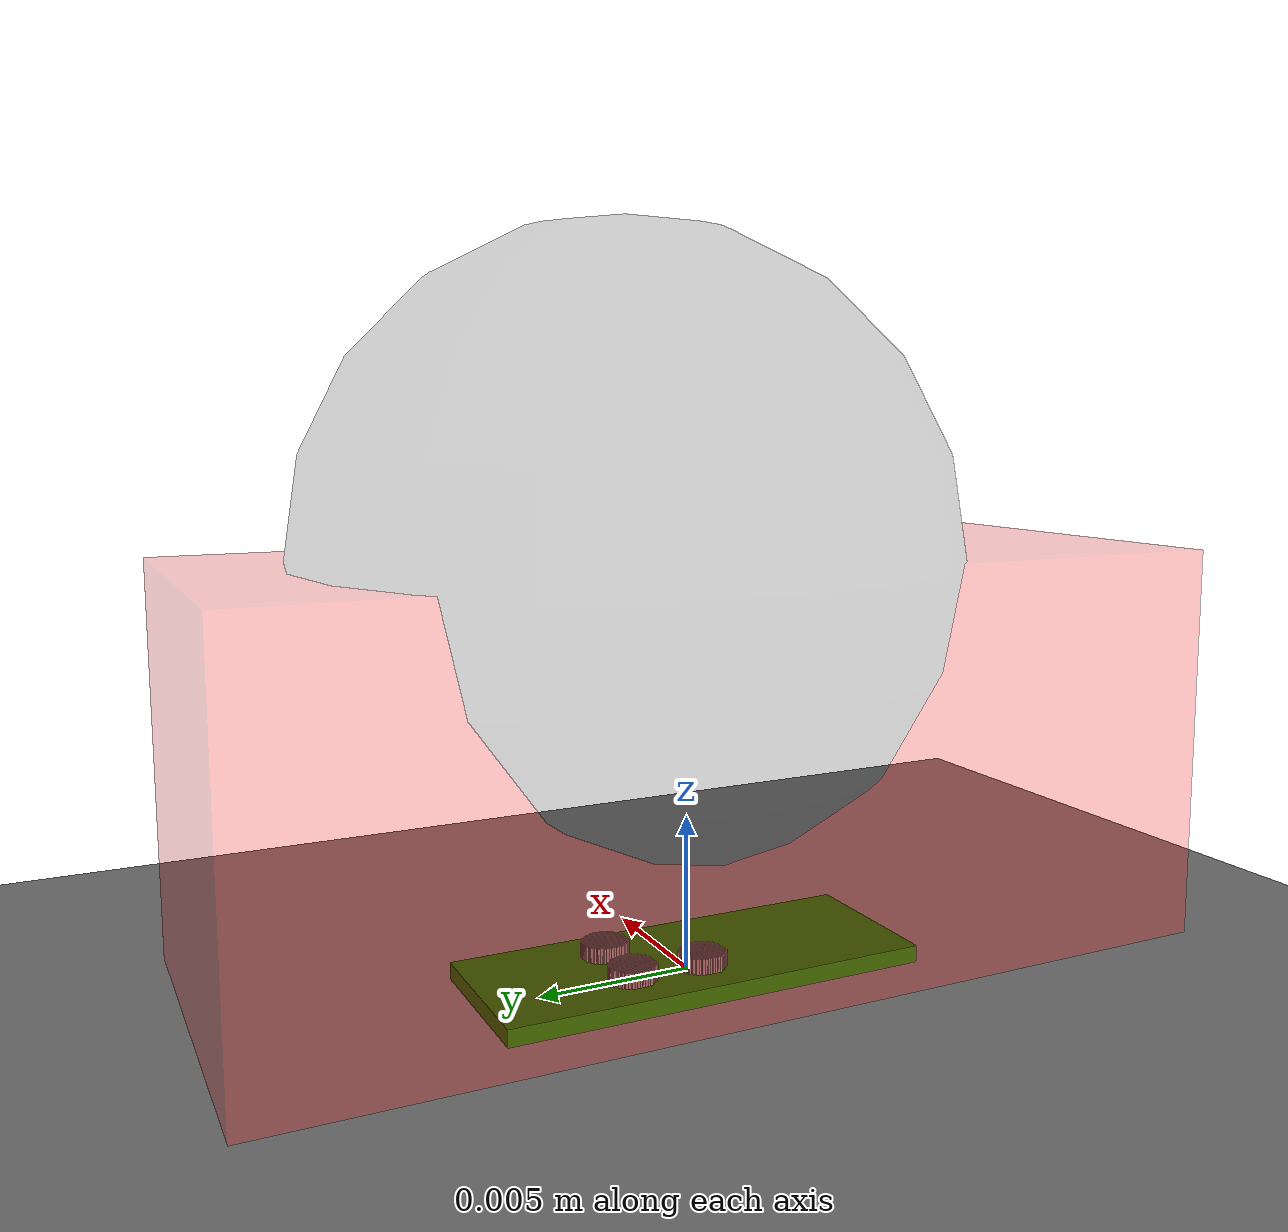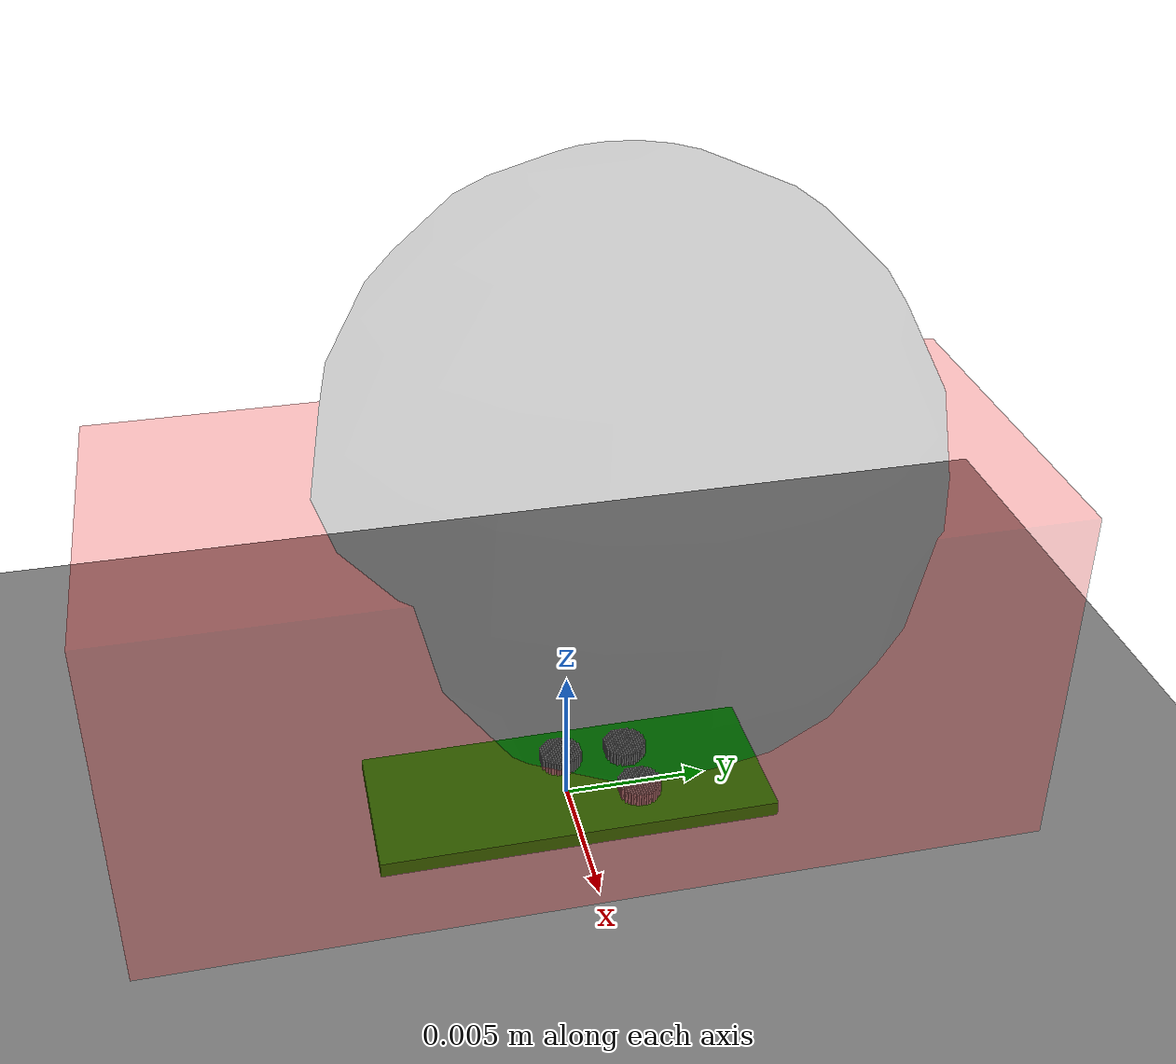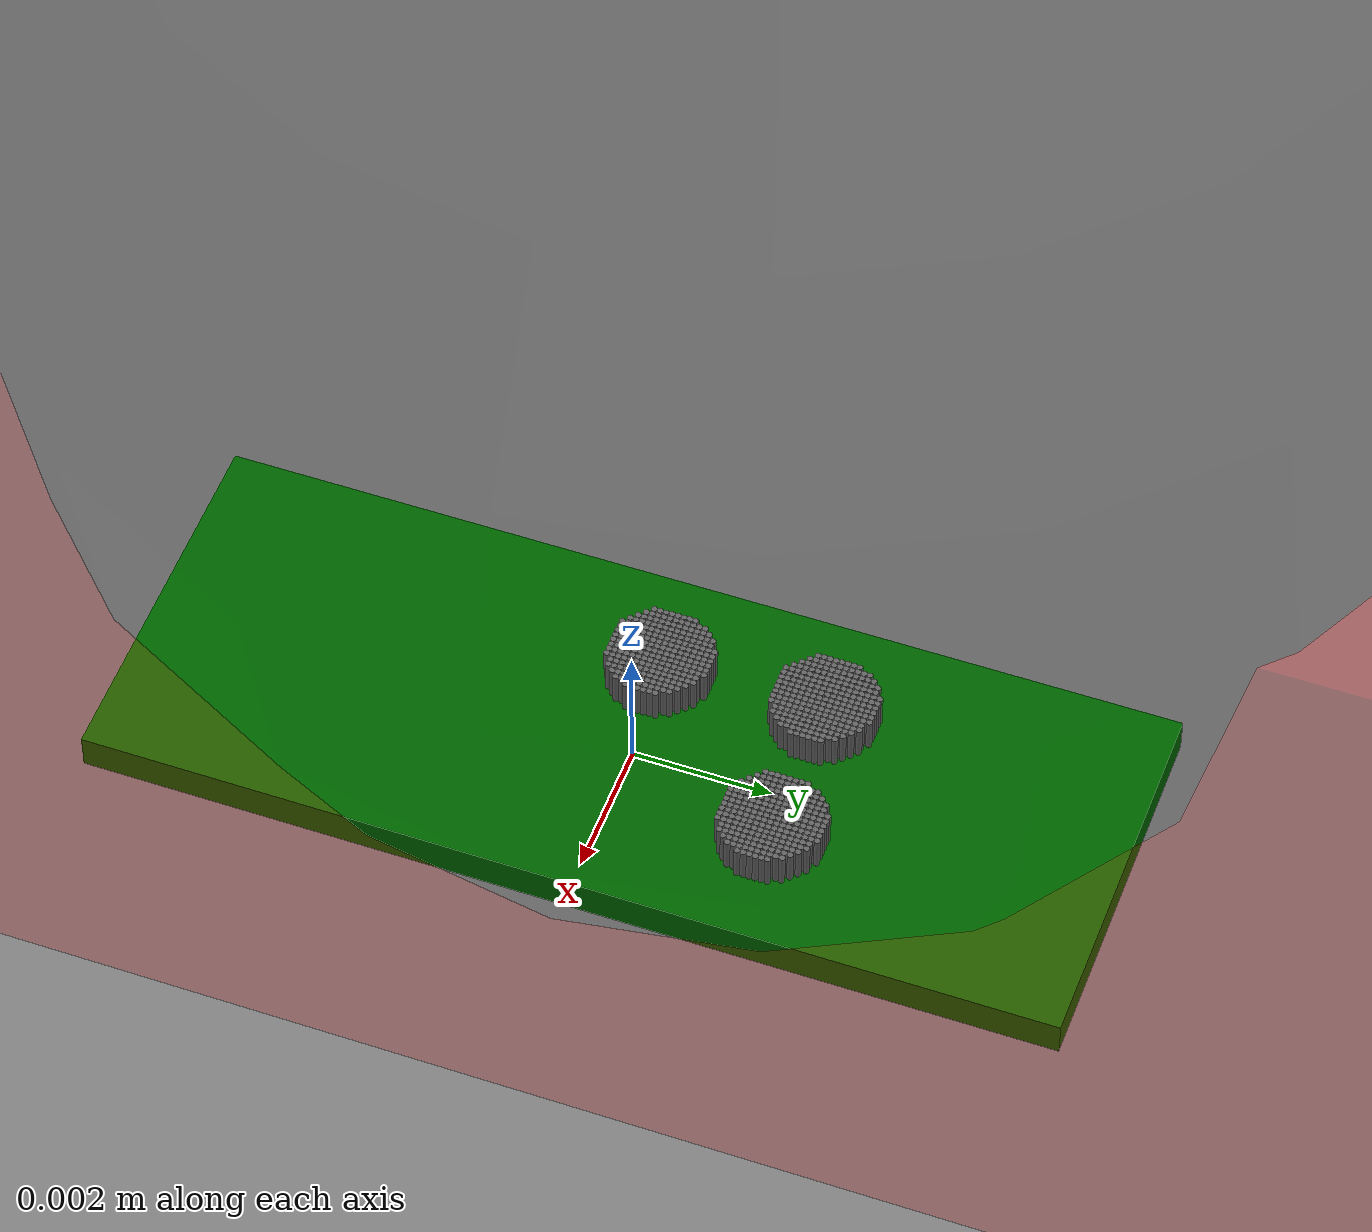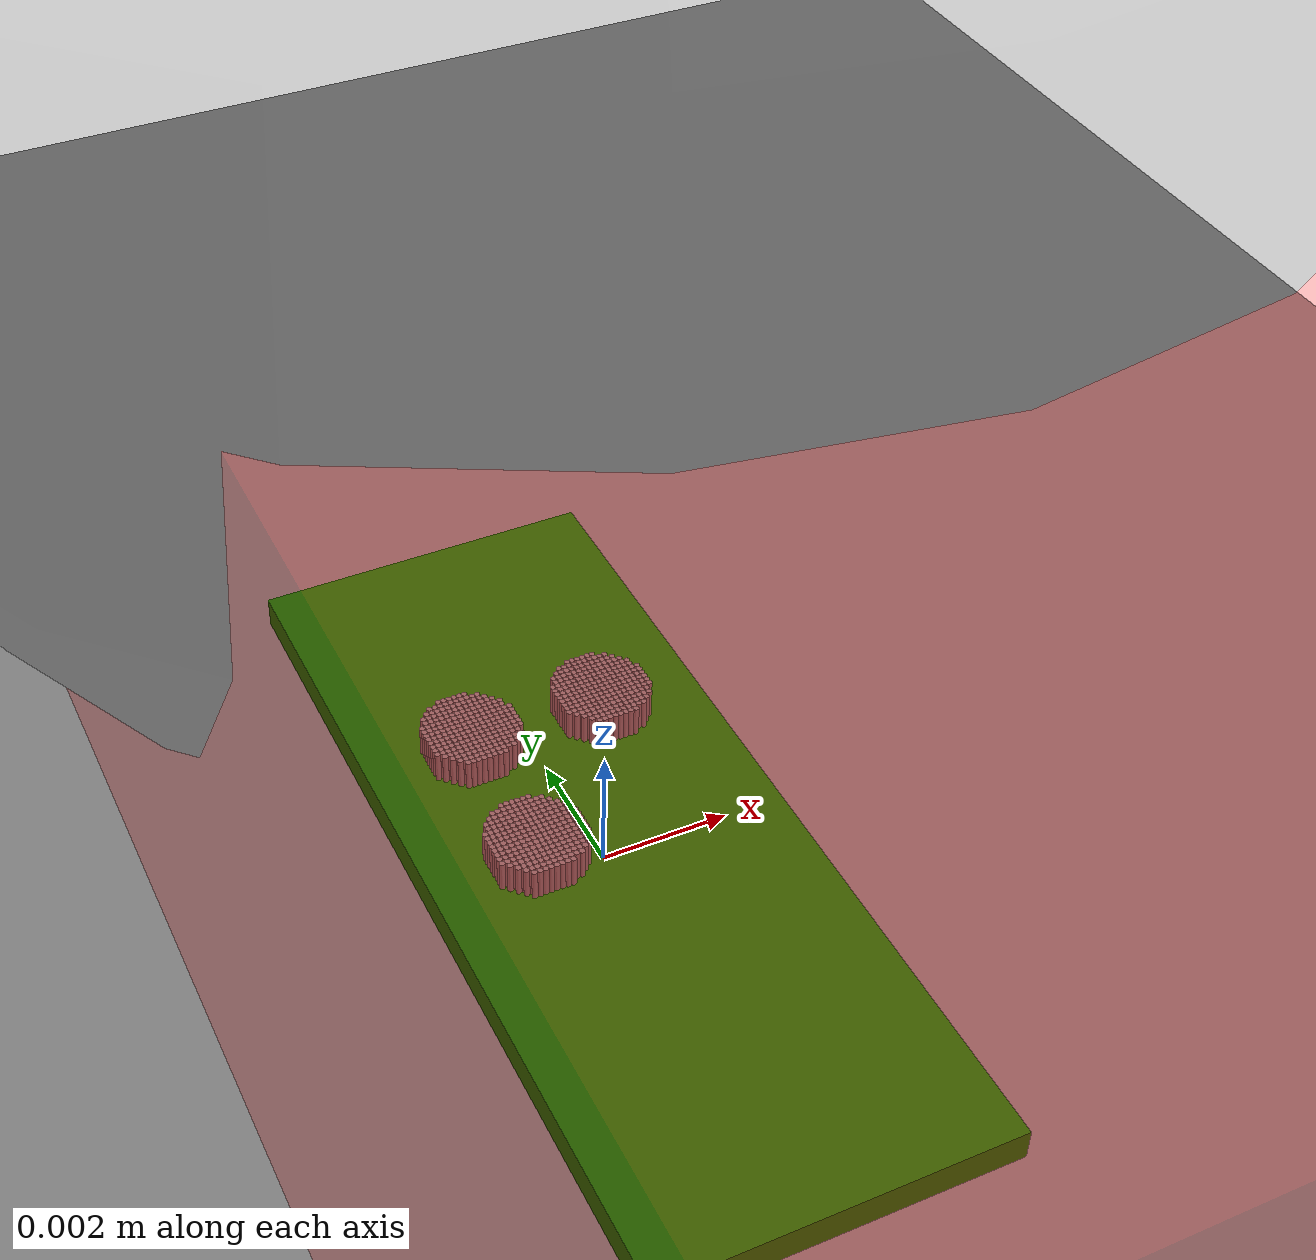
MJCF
<mujoco model="touchtest">
    <compiler autolimits="true" angle='radian'/>

    <extension>
        <plugin plugin="MujocoTactileSensorPlugin"/>
        <plugin plugin="mujoco.sensor.touch_grid"/>
    </extension>

    <option impratio="0.01" timestep='0.01'>
    </option>

    <asset>
        <texture name="grid" type="2d" builtin="checker" rgb1=".1 .2 .3" rgb2=".2 .3 .4" width="300" height="300" mark="edge" markrgb=".2 .3 .4"/>
        <material name="grid" texture="grid" texrepeat="3 1" texuniform="true"/>
        <hfield file="test.png" size="0.0027 0.006955 0.0005 0.00005"/>
        <hfield file="test_dot.png" size="0.00075 0.00075 0.0005 0.00005"/>
        <mesh name="finger_mesh" file="finger.obj" scale='1 1 1'/>
    </asset>

    <visual>
        <headlight ambient=".7 .7 .7" diffuse=".2 .2 .2" specular="0.1 0.1 0.1"/>
        <map znear="0.01"/>
        <scale contactwidth="2" contactheight=".5"/>
    </visual>

    <default>
        <geom friction="0.4" solimp="0.0 0.95 0.02"/>
    </default>

    <statistic center="0 0 1" extent="1" meansize=".1"/>

    <worldbody>
        <light pos="1 0 .3" dir="-1 0 -.3"/>
        <light pos="-1 0 .3" dir="1 0 -.3"/>
        <geom name="floor" pos="0 0 0" type="plane" size="1 1 .01"/>

        <body pos='0 0 0'>

            <geom type='box' size='0.0027 0.006954999999999999 0.0005' rgba='0 0.5 0 1'/>

            <body pos='0 0 0'>
                <geom type='box' size='0.0027 0.006954999999999999 0.0005' rgba='0 0.5 0 1'/>

                <body pos='0.001065 0.00237 0.0005' name='r-top'>

                    <!-- 小さいドットを大量に並べてセンサに引っかかるようにした -->
                    <body pos='0 0 0'>
                        <geom type='cylinder' size='4.2904276540489165e-05 0.0005' pos='-0.0003209572345951085 -0.0006641914469190217 0'/>
                        <geom type='cylinder' size='4.2904276540489165e-05 0.0005' pos='-0.0002351486815141302 -0.0006641914469190217 0'/>
                        <geom type='cylinder' size='4.2904276540489165e-05 0.0005' pos='-0.0001493401284331519 -0.0006641914469190217 0'/>
                        <geom type='cylinder' size='4.2904276540489165e-05 0.0005' pos='-6.353157535217359e-05 -0.0006641914469190217 0'/>
                        <geom type='cylinder' size='4.2904276540489165e-05 0.0005' pos='2.2276977728804713e-05 -0.0006641914469190217 0'/>
                        <geom type='cylinder' size='4.2904276540489165e-05 0.0005' pos='0.00010808553080978302 -0.0006641914469190217 0'/>
                        <geom type='cylinder' size='4.2904276540489165e-05 0.0005' pos='0.00019389408389076132 -0.0006641914469190217 0'/>
                        <geom type='cylinder' size='4.2904276540489165e-05 0.0005' pos='0.0002797026369717396 -0.0006641914469190217 0'/>
                        <geom type='cylinder' size='4.2904276540489165e-05 0.0005' pos='-0.0004067657876760868 -0.0005783828938380434 0'/>
                        <geom type='cylinder' size='4.2904276540489165e-05 0.0005' pos='-0.0003209572345951085 -0.0005783828938380434 0'/>
                        <geom type='cylinder' size='4.2904276540489165e-05 0.0005' pos='-0.0002351486815141302 -0.0005783828938380434 0'/>
                        <geom type='cylinder' size='4.2904276540489165e-05 0.0005' pos='-0.0001493401284331519 -0.0005783828938380434 0'/>
                        <geom type='cylinder' size='4.2904276540489165e-05 0.0005' pos='-6.353157535217359e-05 -0.0005783828938380434 0'/>
                        <geom type='cylinder' size='4.2904276540489165e-05 0.0005' pos='2.2276977728804713e-05 -0.0005783828938380434 0'/>
                        <geom type='cylinder' size='4.2904276540489165e-05 0.0005' pos='0.00010808553080978302 -0.0005783828938380434 0'/>
                        <geom type='cylinder' size='4.2904276540489165e-05 0.0005' pos='0.00019389408389076132 -0.0005783828938380434 0'/>
                        <geom type='cylinder' size='4.2904276540489165e-05 0.0005' pos='0.0002797026369717396 -0.0005783828938380434 0'/>
                        <geom type='cylinder' size='4.2904276540489165e-05 0.0005' pos='0.0003655111900527179 -0.0005783828938380434 0'/>
                        <geom type='cylinder' size='4.2904276540489165e-05 0.0005' pos='0.00045131974313369623 -0.0005783828938380434 0'/>
                        <geom type='cylinder' size='4.2904276540489165e-05 0.0005' pos='-0.0004925743407570651 -0.0004925743407570651 0'/>
                        <geom type='cylinder' size='4.2904276540489165e-05 0.0005' pos='-0.0004067657876760868 -0.0004925743407570651 0'/>
                        <geom type='cylinder' size='4.2904276540489165e-05 0.0005' pos='-0.0003209572345951085 -0.0004925743407570651 0'/>
                        <geom type='cylinder' size='4.2904276540489165e-05 0.0005' pos='-0.0002351486815141302 -0.0004925743407570651 0'/>
                        <geom type='cylinder' size='4.2904276540489165e-05 0.0005' pos='-0.0001493401284331519 -0.0004925743407570651 0'/>
                        <geom type='cylinder' size='4.2904276540489165e-05 0.0005' pos='-6.353157535217359e-05 -0.0004925743407570651 0'/>
                        <geom type='cylinder' size='4.2904276540489165e-05 0.0005' pos='2.2276977728804713e-05 -0.0004925743407570651 0'/>
                        <geom type='cylinder' size='4.2904276540489165e-05 0.0005' pos='0.00010808553080978302 -0.0004925743407570651 0'/>
                        <geom type='cylinder' size='4.2904276540489165e-05 0.0005' pos='0.00019389408389076132 -0.0004925743407570651 0'/>
                        <geom type='cylinder' size='4.2904276540489165e-05 0.0005' pos='0.0002797026369717396 -0.0004925743407570651 0'/>
                        <geom type='cylinder' size='4.2904276540489165e-05 0.0005' pos='0.0003655111900527179 -0.0004925743407570651 0'/>
                        <geom type='cylinder' size='4.2904276540489165e-05 0.0005' pos='0.00045131974313369623 -0.0004925743407570651 0'/>
                        <geom type='cylinder' size='4.2904276540489165e-05 0.0005' pos='0.0005371282962146745 -0.0004925743407570651 0'/>
                        <geom type='cylinder' size='4.2904276540489165e-05 0.0005' pos='-0.0005783828938380434 -0.0004067657876760868 0'/>
                        <geom type='cylinder' size='4.2904276540489165e-05 0.0005' pos='-0.0004925743407570651 -0.0004067657876760868 0'/>
                        <geom type='cylinder' size='4.2904276540489165e-05 0.0005' pos='-0.0004067657876760868 -0.0004067657876760868 0'/>
                        <geom type='cylinder' size='4.2904276540489165e-05 0.0005' pos='-0.0003209572345951085 -0.0004067657876760868 0'/>
                        <geom type='cylinder' size='4.2904276540489165e-05 0.0005' pos='-0.0002351486815141302 -0.0004067657876760868 0'/>
                        <geom type='cylinder' size='4.2904276540489165e-05 0.0005' pos='-0.0001493401284331519 -0.0004067657876760868 0'/>
                        <geom type='cylinder' size='4.2904276540489165e-05 0.0005' pos='-6.353157535217359e-05 -0.0004067657876760868 0'/>
                        <geom type='cylinder' size='4.2904276540489165e-05 0.0005' pos='2.2276977728804713e-05 -0.0004067657876760868 0'/>
                        <geom type='cylinder' size='4.2904276540489165e-05 0.0005' pos='0.00010808553080978302 -0.0004067657876760868 0'/>
                        <geom type='cylinder' size='4.2904276540489165e-05 0.0005' pos='0.00019389408389076132 -0.0004067657876760868 0'/>
                        <geom type='cylinder' size='4.2904276540489165e-05 0.0005' pos='0.0002797026369717396 -0.0004067657876760868 0'/>
                        <geom type='cylinder' size='4.2904276540489165e-05 0.0005' pos='0.0003655111900527179 -0.0004067657876760868 0'/>
                        <geom type='cylinder' size='4.2904276540489165e-05 0.0005' pos='0.00045131974313369623 -0.0004067657876760868 0'/>
                        <geom type='cylinder' size='4.2904276540489165e-05 0.0005' pos='0.0005371282962146745 -0.0004067657876760868 0'/>
                        <geom type='cylinder' size='4.2904276540489165e-05 0.0005' pos='0.0006229368492956528 -0.0004067657876760868 0'/>
                        <geom type='cylinder' size='4.2904276540489165e-05 0.0005' pos='-0.0006641914469190217 -0.0003209572345951085 0'/>
                        <geom type='cylinder' size='4.2904276540489165e-05 0.0005' pos='-0.0005783828938380434 -0.0003209572345951085 0'/>
                        <geom type='cylinder' size='4.2904276540489165e-05 0.0005' pos='-0.0004925743407570651 -0.0003209572345951085 0'/>
                        <geom type='cylinder' size='4.2904276540489165e-05 0.0005' pos='-0.0004067657876760868 -0.0003209572345951085 0'/>
                        <geom type='cylinder' size='4.2904276540489165e-05 0.0005' pos='-0.0003209572345951085 -0.0003209572345951085 0'/>
                        <geom type='cylinder' size='4.2904276540489165e-05 0.0005' pos='-0.0002351486815141302 -0.0003209572345951085 0'/>
                        <geom type='cylinder' size='4.2904276540489165e-05 0.0005' pos='-0.0001493401284331519 -0.0003209572345951085 0'/>
                        <geom type='cylinder' size='4.2904276540489165e-05 0.0005' pos='-6.353157535217359e-05 -0.0003209572345951085 0'/>
                        <geom type='cylinder' size='4.2904276540489165e-05 0.0005' pos='2.2276977728804713e-05 -0.0003209572345951085 0'/>
                        <geom type='cylinder' size='4.2904276540489165e-05 0.0005' pos='0.00010808553080978302 -0.0003209572345951085 0'/>
                        <geom type='cylinder' size='4.2904276540489165e-05 0.0005' pos='0.00019389408389076132 -0.0003209572345951085 0'/>
                        <geom type='cylinder' size='4.2904276540489165e-05 0.0005' pos='0.0002797026369717396 -0.0003209572345951085 0'/>
                        <geom type='cylinder' size='4.2904276540489165e-05 0.0005' pos='0.0003655111900527179 -0.0003209572345951085 0'/>
                        <geom type='cylinder' size='4.2904276540489165e-05 0.0005' pos='0.00045131974313369623 -0.0003209572345951085 0'/>
                        <geom type='cylinder' size='4.2904276540489165e-05 0.0005' pos='0.0005371282962146745 -0.0003209572345951085 0'/>
                        <geom type='cylinder' size='4.2904276540489165e-05 0.0005' pos='0.0006229368492956528 -0.0003209572345951085 0'/>
                        <geom type='cylinder' size='4.2904276540489165e-05 0.0005' pos='-0.0006641914469190217 -0.0002351486815141302 0'/>
                        <geom type='cylinder' size='4.2904276540489165e-05 0.0005' pos='-0.0005783828938380434 -0.0002351486815141302 0'/>
                        <geom type='cylinder' size='4.2904276540489165e-05 0.0005' pos='-0.0004925743407570651 -0.0002351486815141302 0'/>
                        <geom type='cylinder' size='4.2904276540489165e-05 0.0005' pos='-0.0004067657876760868 -0.0002351486815141302 0'/>
                        <geom type='cylinder' size='4.2904276540489165e-05 0.0005' pos='-0.0003209572345951085 -0.0002351486815141302 0'/>
                        <geom type='cylinder' size='4.2904276540489165e-05 0.0005' pos='-0.0002351486815141302 -0.0002351486815141302 0'/>
                        <geom type='cylinder' size='4.2904276540489165e-05 0.0005' pos='-0.0001493401284331519 -0.0002351486815141302 0'/>
                        <geom type='cylinder' size='4.2904276540489165e-05 0.0005' pos='-6.353157535217359e-05 -0.0002351486815141302 0'/>
                        <geom type='cylinder' size='4.2904276540489165e-05 0.0005' pos='2.2276977728804713e-05 -0.0002351486815141302 0'/>
                        <geom type='cylinder' size='4.2904276540489165e-05 0.0005' pos='0.00010808553080978302 -0.0002351486815141302 0'/>
                        <geom type='cylinder' size='4.2904276540489165e-05 0.0005' pos='0.00019389408389076132 -0.0002351486815141302 0'/>
                        <geom type='cylinder' size='4.2904276540489165e-05 0.0005' pos='0.0002797026369717396 -0.0002351486815141302 0'/>
                        <geom type='cylinder' size='4.2904276540489165e-05 0.0005' pos='0.0003655111900527179 -0.0002351486815141302 0'/>
                        <geom type='cylinder' size='4.2904276540489165e-05 0.0005' pos='0.00045131974313369623 -0.0002351486815141302 0'/>
                        <geom type='cylinder' size='4.2904276540489165e-05 0.0005' pos='0.0005371282962146745 -0.0002351486815141302 0'/>
                        <geom type='cylinder' size='4.2904276540489165e-05 0.0005' pos='0.0006229368492956528 -0.0002351486815141302 0'/>
                        <geom type='cylinder' size='4.2904276540489165e-05 0.0005' pos='0.0007087454023766311 -0.0002351486815141302 0'/>
                        <geom type='cylinder' size='4.2904276540489165e-05 0.0005' pos='-0.0006641914469190217 -0.0001493401284331519 0'/>
                        <geom type='cylinder' size='4.2904276540489165e-05 0.0005' pos='-0.0005783828938380434 -0.0001493401284331519 0'/>
                        <geom type='cylinder' size='4.2904276540489165e-05 0.0005' pos='-0.0004925743407570651 -0.0001493401284331519 0'/>
                        <geom type='cylinder' size='4.2904276540489165e-05 0.0005' pos='-0.0004067657876760868 -0.0001493401284331519 0'/>
                        <geom type='cylinder' size='4.2904276540489165e-05 0.0005' pos='-0.0003209572345951085 -0.0001493401284331519 0'/>
                        <geom type='cylinder' size='4.2904276540489165e-05 0.0005' pos='-0.0002351486815141302 -0.0001493401284331519 0'/>
                        <geom type='cylinder' size='4.2904276540489165e-05 0.0005' pos='-0.0001493401284331519 -0.0001493401284331519 0'/>
                        <geom type='cylinder' size='4.2904276540489165e-05 0.0005' pos='-6.353157535217359e-05 -0.0001493401284331519 0'/>
                        <geom type='cylinder' size='4.2904276540489165e-05 0.0005' pos='2.2276977728804713e-05 -0.0001493401284331519 0'/>
                        <geom type='cylinder' size='4.2904276540489165e-05 0.0005' pos='0.00010808553080978302 -0.0001493401284331519 0'/>
                        <geom type='cylinder' size='4.2904276540489165e-05 0.0005' pos='0.00019389408389076132 -0.0001493401284331519 0'/>
                        <geom type='cylinder' size='4.2904276540489165e-05 0.0005' pos='0.0002797026369717396 -0.0001493401284331519 0'/>
                        <geom type='cylinder' size='4.2904276540489165e-05 0.0005' pos='0.0003655111900527179 -0.0001493401284331519 0'/>
                        <geom type='cylinder' size='4.2904276540489165e-05 0.0005' pos='0.00045131974313369623 -0.0001493401284331519 0'/>
                        <geom type='cylinder' size='4.2904276540489165e-05 0.0005' pos='0.0005371282962146745 -0.0001493401284331519 0'/>
                        <geom type='cylinder' size='4.2904276540489165e-05 0.0005' pos='0.0006229368492956528 -0.0001493401284331519 0'/>
                        <geom type='cylinder' size='4.2904276540489165e-05 0.0005' pos='0.0007087454023766311 -0.0001493401284331519 0'/>
                        <geom type='cylinder' size='4.2904276540489165e-05 0.0005' pos='-0.0006641914469190217 -6.353157535217359e-05 0'/>
                        <geom type='cylinder' size='4.2904276540489165e-05 0.0005' pos='-0.0005783828938380434 -6.353157535217359e-05 0'/>
                        <geom type='cylinder' size='4.2904276540489165e-05 0.0005' pos='-0.0004925743407570651 -6.353157535217359e-05 0'/>
                        <geom type='cylinder' size='4.2904276540489165e-05 0.0005' pos='-0.0004067657876760868 -6.353157535217359e-05 0'/>
                        <geom type='cylinder' size='4.2904276540489165e-05 0.0005' pos='-0.0003209572345951085 -6.353157535217359e-05 0'/>
                        <geom type='cylinder' size='4.2904276540489165e-05 0.0005' pos='-0.0002351486815141302 -6.353157535217359e-05 0'/>
                        <geom type='cylinder' size='4.2904276540489165e-05 0.0005' pos='-0.0001493401284331519 -6.353157535217359e-05 0'/>
                        <geom type='cylinder' size='4.2904276540489165e-05 0.0005' pos='-6.353157535217359e-05 -6.353157535217359e-05 0'/>
                        <geom type='cylinder' size='4.2904276540489165e-05 0.0005' pos='2.2276977728804713e-05 -6.353157535217359e-05 0'/>
                        <geom type='cylinder' size='4.2904276540489165e-05 0.0005' pos='0.00010808553080978302 -6.353157535217359e-05 0'/>
                        <geom type='cylinder' size='4.2904276540489165e-05 0.0005' pos='0.00019389408389076132 -6.353157535217359e-05 0'/>
                        <geom type='cylinder' size='4.2904276540489165e-05 0.0005' pos='0.0002797026369717396 -6.353157535217359e-05 0'/>
                        <geom type='cylinder' size='4.2904276540489165e-05 0.0005' pos='0.0003655111900527179 -6.353157535217359e-05 0'/>
                        <geom type='cylinder' size='4.2904276540489165e-05 0.0005' pos='0.00045131974313369623 -6.353157535217359e-05 0'/>
                        <geom type='cylinder' size='4.2904276540489165e-05 0.0005' pos='0.0005371282962146745 -6.353157535217359e-05 0'/>
                        <geom type='cylinder' size='4.2904276540489165e-05 0.0005' pos='0.0006229368492956528 -6.353157535217359e-05 0'/>
                        <geom type='cylinder' size='4.2904276540489165e-05 0.0005' pos='0.0007087454023766311 -6.353157535217359e-05 0'/>
                        <geom type='cylinder' size='4.2904276540489165e-05 0.0005' pos='-0.0006641914469190217 2.2276977728804713e-05 0'/>
                        <geom type='cylinder' size='4.2904276540489165e-05 0.0005' pos='-0.0005783828938380434 2.2276977728804713e-05 0'/>
                        <geom type='cylinder' size='4.2904276540489165e-05 0.0005' pos='-0.0004925743407570651 2.2276977728804713e-05 0'/>
                        <geom type='cylinder' size='4.2904276540489165e-05 0.0005' pos='-0.0004067657876760868 2.2276977728804713e-05 0'/>
                        <geom type='cylinder' size='4.2904276540489165e-05 0.0005' pos='-0.0003209572345951085 2.2276977728804713e-05 0'/>
                        <geom type='cylinder' size='4.2904276540489165e-05 0.0005' pos='-0.0002351486815141302 2.2276977728804713e-05 0'/>
                        <geom type='cylinder' size='4.2904276540489165e-05 0.0005' pos='-0.0001493401284331519 2.2276977728804713e-05 0'/>
                        <geom type='cylinder' size='4.2904276540489165e-05 0.0005' pos='-6.353157535217359e-05 2.2276977728804713e-05 0'/>
                        <geom type='cylinder' size='4.2904276540489165e-05 0.0005' pos='2.2276977728804713e-05 2.2276977728804713e-05 0'/>
                        <geom type='cylinder' size='4.2904276540489165e-05 0.0005' pos='0.00010808553080978302 2.2276977728804713e-05 0'/>
                        <geom type='cylinder' size='4.2904276540489165e-05 0.0005' pos='0.00019389408389076132 2.2276977728804713e-05 0'/>
                        <geom type='cylinder' size='4.2904276540489165e-05 0.0005' pos='0.0002797026369717396 2.2276977728804713e-05 0'/>
                        <geom type='cylinder' size='4.2904276540489165e-05 0.0005' pos='0.0003655111900527179 2.2276977728804713e-05 0'/>
                        <geom type='cylinder' size='4.2904276540489165e-05 0.0005' pos='0.00045131974313369623 2.2276977728804713e-05 0'/>
                        <geom type='cylinder' size='4.2904276540489165e-05 0.0005' pos='0.0005371282962146745 2.2276977728804713e-05 0'/>
                        <geom type='cylinder' size='4.2904276540489165e-05 0.0005' pos='0.0006229368492956528 2.2276977728804713e-05 0'/>
                        <geom type='cylinder' size='4.2904276540489165e-05 0.0005' pos='0.0007087454023766311 2.2276977728804713e-05 0'/>
                        <geom type='cylinder' size='4.2904276540489165e-05 0.0005' pos='-0.0006641914469190217 0.00010808553080978302 0'/>
                        <geom type='cylinder' size='4.2904276540489165e-05 0.0005' pos='-0.0005783828938380434 0.00010808553080978302 0'/>
                        <geom type='cylinder' size='4.2904276540489165e-05 0.0005' pos='-0.0004925743407570651 0.00010808553080978302 0'/>
                        <geom type='cylinder' size='4.2904276540489165e-05 0.0005' pos='-0.0004067657876760868 0.00010808553080978302 0'/>
                        <geom type='cylinder' size='4.2904276540489165e-05 0.0005' pos='-0.0003209572345951085 0.00010808553080978302 0'/>
                        <geom type='cylinder' size='4.2904276540489165e-05 0.0005' pos='-0.0002351486815141302 0.00010808553080978302 0'/>
                        <geom type='cylinder' size='4.2904276540489165e-05 0.0005' pos='-0.0001493401284331519 0.00010808553080978302 0'/>
                        <geom type='cylinder' size='4.2904276540489165e-05 0.0005' pos='-6.353157535217359e-05 0.00010808553080978302 0'/>
                        <geom type='cylinder' size='4.2904276540489165e-05 0.0005' pos='2.2276977728804713e-05 0.00010808553080978302 0'/>
                        <geom type='cylinder' size='4.2904276540489165e-05 0.0005' pos='0.00010808553080978302 0.00010808553080978302 0'/>
                        <geom type='cylinder' size='4.2904276540489165e-05 0.0005' pos='0.00019389408389076132 0.00010808553080978302 0'/>
                        <geom type='cylinder' size='4.2904276540489165e-05 0.0005' pos='0.0002797026369717396 0.00010808553080978302 0'/>
                        <geom type='cylinder' size='4.2904276540489165e-05 0.0005' pos='0.0003655111900527179 0.00010808553080978302 0'/>
                        <geom type='cylinder' size='4.2904276540489165e-05 0.0005' pos='0.00045131974313369623 0.00010808553080978302 0'/>
                        <geom type='cylinder' size='4.2904276540489165e-05 0.0005' pos='0.0005371282962146745 0.00010808553080978302 0'/>
                        <geom type='cylinder' size='4.2904276540489165e-05 0.0005' pos='0.0006229368492956528 0.00010808553080978302 0'/>
                        <geom type='cylinder' size='4.2904276540489165e-05 0.0005' pos='0.0007087454023766311 0.00010808553080978302 0'/>
                        <geom type='cylinder' size='4.2904276540489165e-05 0.0005' pos='-0.0006641914469190217 0.00019389408389076132 0'/>
                        <geom type='cylinder' size='4.2904276540489165e-05 0.0005' pos='-0.0005783828938380434 0.00019389408389076132 0'/>
                        <geom type='cylinder' size='4.2904276540489165e-05 0.0005' pos='-0.0004925743407570651 0.00019389408389076132 0'/>
                        <geom type='cylinder' size='4.2904276540489165e-05 0.0005' pos='-0.0004067657876760868 0.00019389408389076132 0'/>
                        <geom type='cylinder' size='4.2904276540489165e-05 0.0005' pos='-0.0003209572345951085 0.00019389408389076132 0'/>
                        <geom type='cylinder' size='4.2904276540489165e-05 0.0005' pos='-0.0002351486815141302 0.00019389408389076132 0'/>
                        <geom type='cylinder' size='4.2904276540489165e-05 0.0005' pos='-0.0001493401284331519 0.00019389408389076132 0'/>
                        <geom type='cylinder' size='4.2904276540489165e-05 0.0005' pos='-6.353157535217359e-05 0.00019389408389076132 0'/>
                        <geom type='cylinder' size='4.2904276540489165e-05 0.0005' pos='2.2276977728804713e-05 0.00019389408389076132 0'/>
                        <geom type='cylinder' size='4.2904276540489165e-05 0.0005' pos='0.00010808553080978302 0.00019389408389076132 0'/>
                        <geom type='cylinder' size='4.2904276540489165e-05 0.0005' pos='0.00019389408389076132 0.00019389408389076132 0'/>
                        <geom type='cylinder' size='4.2904276540489165e-05 0.0005' pos='0.0002797026369717396 0.00019389408389076132 0'/>
                        <geom type='cylinder' size='4.2904276540489165e-05 0.0005' pos='0.0003655111900527179 0.00019389408389076132 0'/>
                        <geom type='cylinder' size='4.2904276540489165e-05 0.0005' pos='0.00045131974313369623 0.00019389408389076132 0'/>
                        <geom type='cylinder' size='4.2904276540489165e-05 0.0005' pos='0.0005371282962146745 0.00019389408389076132 0'/>
                        <geom type='cylinder' size='4.2904276540489165e-05 0.0005' pos='0.0006229368492956528 0.00019389408389076132 0'/>
                        <geom type='cylinder' size='4.2904276540489165e-05 0.0005' pos='0.0007087454023766311 0.00019389408389076132 0'/>
                        <geom type='cylinder' size='4.2904276540489165e-05 0.0005' pos='-0.0006641914469190217 0.0002797026369717396 0'/>
                        <geom type='cylinder' size='4.2904276540489165e-05 0.0005' pos='-0.0005783828938380434 0.0002797026369717396 0'/>
                        <geom type='cylinder' size='4.2904276540489165e-05 0.0005' pos='-0.0004925743407570651 0.0002797026369717396 0'/>
                        <geom type='cylinder' size='4.2904276540489165e-05 0.0005' pos='-0.0004067657876760868 0.0002797026369717396 0'/>
                        <geom type='cylinder' size='4.2904276540489165e-05 0.0005' pos='-0.0003209572345951085 0.0002797026369717396 0'/>
                        <geom type='cylinder' size='4.2904276540489165e-05 0.0005' pos='-0.0002351486815141302 0.0002797026369717396 0'/>
                        <geom type='cylinder' size='4.2904276540489165e-05 0.0005' pos='-0.0001493401284331519 0.0002797026369717396 0'/>
                        <geom type='cylinder' size='4.2904276540489165e-05 0.0005' pos='-6.353157535217359e-05 0.0002797026369717396 0'/>
                        <geom type='cylinder' size='4.2904276540489165e-05 0.0005' pos='2.2276977728804713e-05 0.0002797026369717396 0'/>
                        <geom type='cylinder' size='4.2904276540489165e-05 0.0005' pos='0.00010808553080978302 0.0002797026369717396 0'/>
                        <geom type='cylinder' size='4.2904276540489165e-05 0.0005' pos='0.00019389408389076132 0.0002797026369717396 0'/>
                        <geom type='cylinder' size='4.2904276540489165e-05 0.0005' pos='0.0002797026369717396 0.0002797026369717396 0'/>
                        <geom type='cylinder' size='4.2904276540489165e-05 0.0005' pos='0.0003655111900527179 0.0002797026369717396 0'/>
                        <geom type='cylinder' size='4.2904276540489165e-05 0.0005' pos='0.00045131974313369623 0.0002797026369717396 0'/>
                        <geom type='cylinder' size='4.2904276540489165e-05 0.0005' pos='0.0005371282962146745 0.0002797026369717396 0'/>
                        <geom type='cylinder' size='4.2904276540489165e-05 0.0005' pos='0.0006229368492956528 0.0002797026369717396 0'/>
                        <geom type='cylinder' size='4.2904276540489165e-05 0.0005' pos='-0.0005783828938380434 0.0003655111900527179 0'/>
                        <geom type='cylinder' size='4.2904276540489165e-05 0.0005' pos='-0.0004925743407570651 0.0003655111900527179 0'/>
                        <geom type='cylinder' size='4.2904276540489165e-05 0.0005' pos='-0.0004067657876760868 0.0003655111900527179 0'/>
                        <geom type='cylinder' size='4.2904276540489165e-05 0.0005' pos='-0.0003209572345951085 0.0003655111900527179 0'/>
                        <geom type='cylinder' size='4.2904276540489165e-05 0.0005' pos='-0.0002351486815141302 0.0003655111900527179 0'/>
                        <geom type='cylinder' size='4.2904276540489165e-05 0.0005' pos='-0.0001493401284331519 0.0003655111900527179 0'/>
                        <geom type='cylinder' size='4.2904276540489165e-05 0.0005' pos='-6.353157535217359e-05 0.0003655111900527179 0'/>
                        <geom type='cylinder' size='4.2904276540489165e-05 0.0005' pos='2.2276977728804713e-05 0.0003655111900527179 0'/>
                        <geom type='cylinder' size='4.2904276540489165e-05 0.0005' pos='0.00010808553080978302 0.0003655111900527179 0'/>
                        <geom type='cylinder' size='4.2904276540489165e-05 0.0005' pos='0.00019389408389076132 0.0003655111900527179 0'/>
                        <geom type='cylinder' size='4.2904276540489165e-05 0.0005' pos='0.0002797026369717396 0.0003655111900527179 0'/>
                        <geom type='cylinder' size='4.2904276540489165e-05 0.0005' pos='0.0003655111900527179 0.0003655111900527179 0'/>
                        <geom type='cylinder' size='4.2904276540489165e-05 0.0005' pos='0.00045131974313369623 0.0003655111900527179 0'/>
                        <geom type='cylinder' size='4.2904276540489165e-05 0.0005' pos='0.0005371282962146745 0.0003655111900527179 0'/>
                        <geom type='cylinder' size='4.2904276540489165e-05 0.0005' pos='0.0006229368492956528 0.0003655111900527179 0'/>
                        <geom type='cylinder' size='4.2904276540489165e-05 0.0005' pos='-0.0005783828938380434 0.00045131974313369623 0'/>
                        <geom type='cylinder' size='4.2904276540489165e-05 0.0005' pos='-0.0004925743407570651 0.00045131974313369623 0'/>
                        <geom type='cylinder' size='4.2904276540489165e-05 0.0005' pos='-0.0004067657876760868 0.00045131974313369623 0'/>
                        <geom type='cylinder' size='4.2904276540489165e-05 0.0005' pos='-0.0003209572345951085 0.00045131974313369623 0'/>
                        <geom type='cylinder' size='4.2904276540489165e-05 0.0005' pos='-0.0002351486815141302 0.00045131974313369623 0'/>
                        <geom type='cylinder' size='4.2904276540489165e-05 0.0005' pos='-0.0001493401284331519 0.00045131974313369623 0'/>
                        <geom type='cylinder' size='4.2904276540489165e-05 0.0005' pos='-6.353157535217359e-05 0.00045131974313369623 0'/>
                        <geom type='cylinder' size='4.2904276540489165e-05 0.0005' pos='2.2276977728804713e-05 0.00045131974313369623 0'/>
                        <geom type='cylinder' size='4.2904276540489165e-05 0.0005' pos='0.00010808553080978302 0.00045131974313369623 0'/>
                        <geom type='cylinder' size='4.2904276540489165e-05 0.0005' pos='0.00019389408389076132 0.00045131974313369623 0'/>
                        <geom type='cylinder' size='4.2904276540489165e-05 0.0005' pos='0.0002797026369717396 0.00045131974313369623 0'/>
                        <geom type='cylinder' size='4.2904276540489165e-05 0.0005' pos='0.0003655111900527179 0.00045131974313369623 0'/>
                        <geom type='cylinder' size='4.2904276540489165e-05 0.0005' pos='0.00045131974313369623 0.00045131974313369623 0'/>
                        <geom type='cylinder' size='4.2904276540489165e-05 0.0005' pos='0.0005371282962146745 0.00045131974313369623 0'/>
                        <geom type='cylinder' size='4.2904276540489165e-05 0.0005' pos='-0.0004925743407570651 0.0005371282962146745 0'/>
                        <geom type='cylinder' size='4.2904276540489165e-05 0.0005' pos='-0.0004067657876760868 0.0005371282962146745 0'/>
                        <geom type='cylinder' size='4.2904276540489165e-05 0.0005' pos='-0.0003209572345951085 0.0005371282962146745 0'/>
                        <geom type='cylinder' size='4.2904276540489165e-05 0.0005' pos='-0.0002351486815141302 0.0005371282962146745 0'/>
                        <geom type='cylinder' size='4.2904276540489165e-05 0.0005' pos='-0.0001493401284331519 0.0005371282962146745 0'/>
                        <geom type='cylinder' size='4.2904276540489165e-05 0.0005' pos='-6.353157535217359e-05 0.0005371282962146745 0'/>
                        <geom type='cylinder' size='4.2904276540489165e-05 0.0005' pos='2.2276977728804713e-05 0.0005371282962146745 0'/>
                        <geom type='cylinder' size='4.2904276540489165e-05 0.0005' pos='0.00010808553080978302 0.0005371282962146745 0'/>
                        <geom type='cylinder' size='4.2904276540489165e-05 0.0005' pos='0.00019389408389076132 0.0005371282962146745 0'/>
                        <geom type='cylinder' size='4.2904276540489165e-05 0.0005' pos='0.0002797026369717396 0.0005371282962146745 0'/>
                        <geom type='cylinder' size='4.2904276540489165e-05 0.0005' pos='0.0003655111900527179 0.0005371282962146745 0'/>
                        <geom type='cylinder' size='4.2904276540489165e-05 0.0005' pos='0.00045131974313369623 0.0005371282962146745 0'/>
                        <geom type='cylinder' size='4.2904276540489165e-05 0.0005' pos='-0.0004067657876760868 0.0006229368492956528 0'/>
                        <geom type='cylinder' size='4.2904276540489165e-05 0.0005' pos='-0.0003209572345951085 0.0006229368492956528 0'/>
                        <geom type='cylinder' size='4.2904276540489165e-05 0.0005' pos='-0.0002351486815141302 0.0006229368492956528 0'/>
                        <geom type='cylinder' size='4.2904276540489165e-05 0.0005' pos='-0.0001493401284331519 0.0006229368492956528 0'/>
                        <geom type='cylinder' size='4.2904276540489165e-05 0.0005' pos='-6.353157535217359e-05 0.0006229368492956528 0'/>
                        <geom type='cylinder' size='4.2904276540489165e-05 0.0005' pos='2.2276977728804713e-05 0.0006229368492956528 0'/>
                        <geom type='cylinder' size='4.2904276540489165e-05 0.0005' pos='0.00010808553080978302 0.0006229368492956528 0'/>
                        <geom type='cylinder' size='4.2904276540489165e-05 0.0005' pos='0.00019389408389076132 0.0006229368492956528 0'/>
                        <geom type='cylinder' size='4.2904276540489165e-05 0.0005' pos='0.0002797026369717396 0.0006229368492956528 0'/>
                        <geom type='cylinder' size='4.2904276540489165e-05 0.0005' pos='0.0003655111900527179 0.0006229368492956528 0'/>
                        <geom type='cylinder' size='4.2904276540489165e-05 0.0005' pos='-0.0002351486815141302 0.0007087454023766311 0'/>
                        <geom type='cylinder' size='4.2904276540489165e-05 0.0005' pos='-0.0001493401284331519 0.0007087454023766311 0'/>
                        <geom type='cylinder' size='4.2904276540489165e-05 0.0005' pos='-6.353157535217359e-05 0.0007087454023766311 0'/>
                        <geom type='cylinder' size='4.2904276540489165e-05 0.0005' pos='2.2276977728804713e-05 0.0007087454023766311 0'/>
                        <geom type='cylinder' size='4.2904276540489165e-05 0.0005' pos='0.00010808553080978302 0.0007087454023766311 0'/>
                        <geom type='cylinder' size='4.2904276540489165e-05 0.0005' pos='0.00019389408389076132 0.0007087454023766311 0'/>

                    </body>
                    <!-- 小さいドットを大量に並べてセンサに引っかかるようにした -->

                </body>
                <body pos='-0.001065 0.00237 0.0005' name='l-top'>

                    <body pos='0 0 0'>
                        <geom type='cylinder' size='4.2904276540489165e-05 0.0005' pos='-0.0003209572345951085 -0.0006641914469190217 0'/>
                        <geom type='cylinder' size='4.2904276540489165e-05 0.0005' pos='-0.0002351486815141302 -0.0006641914469190217 0'/>
                        <geom type='cylinder' size='4.2904276540489165e-05 0.0005' pos='-0.0001493401284331519 -0.0006641914469190217 0'/>
                        <geom type='cylinder' size='4.2904276540489165e-05 0.0005' pos='-6.353157535217359e-05 -0.0006641914469190217 0'/>
                        <geom type='cylinder' size='4.2904276540489165e-05 0.0005' pos='2.2276977728804713e-05 -0.0006641914469190217 0'/>
                        <geom type='cylinder' size='4.2904276540489165e-05 0.0005' pos='0.00010808553080978302 -0.0006641914469190217 0'/>
                        <geom type='cylinder' size='4.2904276540489165e-05 0.0005' pos='0.00019389408389076132 -0.0006641914469190217 0'/>
                        <geom type='cylinder' size='4.2904276540489165e-05 0.0005' pos='0.0002797026369717396 -0.0006641914469190217 0'/>
                        <geom type='cylinder' size='4.2904276540489165e-05 0.0005' pos='-0.0004067657876760868 -0.0005783828938380434 0'/>
                        <geom type='cylinder' size='4.2904276540489165e-05 0.0005' pos='-0.0003209572345951085 -0.0005783828938380434 0'/>
                        <geom type='cylinder' size='4.2904276540489165e-05 0.0005' pos='-0.0002351486815141302 -0.0005783828938380434 0'/>
                        <geom type='cylinder' size='4.2904276540489165e-05 0.0005' pos='-0.0001493401284331519 -0.0005783828938380434 0'/>
                        <geom type='cylinder' size='4.2904276540489165e-05 0.0005' pos='-6.353157535217359e-05 -0.0005783828938380434 0'/>
                        <geom type='cylinder' size='4.2904276540489165e-05 0.0005' pos='2.2276977728804713e-05 -0.0005783828938380434 0'/>
                        <geom type='cylinder' size='4.2904276540489165e-05 0.0005' pos='0.00010808553080978302 -0.0005783828938380434 0'/>
                        <geom type='cylinder' size='4.2904276540489165e-05 0.0005' pos='0.00019389408389076132 -0.0005783828938380434 0'/>
                        <geom type='cylinder' size='4.2904276540489165e-05 0.0005' pos='0.0002797026369717396 -0.0005783828938380434 0'/>
                        <geom type='cylinder' size='4.2904276540489165e-05 0.0005' pos='0.0003655111900527179 -0.0005783828938380434 0'/>
                        <geom type='cylinder' size='4.2904276540489165e-05 0.0005' pos='0.00045131974313369623 -0.0005783828938380434 0'/>
                        <geom type='cylinder' size='4.2904276540489165e-05 0.0005' pos='-0.0004925743407570651 -0.0004925743407570651 0'/>
                        <geom type='cylinder' size='4.2904276540489165e-05 0.0005' pos='-0.0004067657876760868 -0.0004925743407570651 0'/>
                        <geom type='cylinder' size='4.2904276540489165e-05 0.0005' pos='-0.0003209572345951085 -0.0004925743407570651 0'/>
                        <geom type='cylinder' size='4.2904276540489165e-05 0.0005' pos='-0.0002351486815141302 -0.0004925743407570651 0'/>
                        <geom type='cylinder' size='4.2904276540489165e-05 0.0005' pos='-0.0001493401284331519 -0.0004925743407570651 0'/>
                        <geom type='cylinder' size='4.2904276540489165e-05 0.0005' pos='-6.353157535217359e-05 -0.0004925743407570651 0'/>
                        <geom type='cylinder' size='4.2904276540489165e-05 0.0005' pos='2.2276977728804713e-05 -0.0004925743407570651 0'/>
                        <geom type='cylinder' size='4.2904276540489165e-05 0.0005' pos='0.00010808553080978302 -0.0004925743407570651 0'/>
                        <geom type='cylinder' size='4.2904276540489165e-05 0.0005' pos='0.00019389408389076132 -0.0004925743407570651 0'/>
                        <geom type='cylinder' size='4.2904276540489165e-05 0.0005' pos='0.0002797026369717396 -0.0004925743407570651 0'/>
                        <geom type='cylinder' size='4.2904276540489165e-05 0.0005' pos='0.0003655111900527179 -0.0004925743407570651 0'/>
                        <geom type='cylinder' size='4.2904276540489165e-05 0.0005' pos='0.00045131974313369623 -0.0004925743407570651 0'/>
                        <geom type='cylinder' size='4.2904276540489165e-05 0.0005' pos='0.0005371282962146745 -0.0004925743407570651 0'/>
                        <geom type='cylinder' size='4.2904276540489165e-05 0.0005' pos='-0.0005783828938380434 -0.0004067657876760868 0'/>
                        <geom type='cylinder' size='4.2904276540489165e-05 0.0005' pos='-0.0004925743407570651 -0.0004067657876760868 0'/>
                        <geom type='cylinder' size='4.2904276540489165e-05 0.0005' pos='-0.0004067657876760868 -0.0004067657876760868 0'/>
                        <geom type='cylinder' size='4.2904276540489165e-05 0.0005' pos='-0.0003209572345951085 -0.0004067657876760868 0'/>
                        <geom type='cylinder' size='4.2904276540489165e-05 0.0005' pos='-0.0002351486815141302 -0.0004067657876760868 0'/>
                        <geom type='cylinder' size='4.2904276540489165e-05 0.0005' pos='-0.0001493401284331519 -0.0004067657876760868 0'/>
                        <geom type='cylinder' size='4.2904276540489165e-05 0.0005' pos='-6.353157535217359e-05 -0.0004067657876760868 0'/>
                        <geom type='cylinder' size='4.2904276540489165e-05 0.0005' pos='2.2276977728804713e-05 -0.0004067657876760868 0'/>
                        <geom type='cylinder' size='4.2904276540489165e-05 0.0005' pos='0.00010808553080978302 -0.0004067657876760868 0'/>
                        <geom type='cylinder' size='4.2904276540489165e-05 0.0005' pos='0.00019389408389076132 -0.0004067657876760868 0'/>
                        <geom type='cylinder' size='4.2904276540489165e-05 0.0005' pos='0.0002797026369717396 -0.0004067657876760868 0'/>
                        <geom type='cylinder' size='4.2904276540489165e-05 0.0005' pos='0.0003655111900527179 -0.0004067657876760868 0'/>
                        <geom type='cylinder' size='4.2904276540489165e-05 0.0005' pos='0.00045131974313369623 -0.0004067657876760868 0'/>
                        <geom type='cylinder' size='4.2904276540489165e-05 0.0005' pos='0.0005371282962146745 -0.0004067657876760868 0'/>
                        <geom type='cylinder' size='4.2904276540489165e-05 0.0005' pos='0.0006229368492956528 -0.0004067657876760868 0'/>
                        <geom type='cylinder' size='4.2904276540489165e-05 0.0005' pos='-0.0006641914469190217 -0.0003209572345951085 0'/>
                        <geom type='cylinder' size='4.2904276540489165e-05 0.0005' pos='-0.0005783828938380434 -0.0003209572345951085 0'/>
                        <geom type='cylinder' size='4.2904276540489165e-05 0.0005' pos='-0.0004925743407570651 -0.0003209572345951085 0'/>
                        <geom type='cylinder' size='4.2904276540489165e-05 0.0005' pos='-0.0004067657876760868 -0.0003209572345951085 0'/>
                        <geom type='cylinder' size='4.2904276540489165e-05 0.0005' pos='-0.0003209572345951085 -0.0003209572345951085 0'/>
                        <geom type='cylinder' size='4.2904276540489165e-05 0.0005' pos='-0.0002351486815141302 -0.0003209572345951085 0'/>
                        <geom type='cylinder' size='4.2904276540489165e-05 0.0005' pos='-0.0001493401284331519 -0.0003209572345951085 0'/>
                        <geom type='cylinder' size='4.2904276540489165e-05 0.0005' pos='-6.353157535217359e-05 -0.0003209572345951085 0'/>
                        <geom type='cylinder' size='4.2904276540489165e-05 0.0005' pos='2.2276977728804713e-05 -0.0003209572345951085 0'/>
                        <geom type='cylinder' size='4.2904276540489165e-05 0.0005' pos='0.00010808553080978302 -0.0003209572345951085 0'/>
                        <geom type='cylinder' size='4.2904276540489165e-05 0.0005' pos='0.00019389408389076132 -0.0003209572345951085 0'/>
                        <geom type='cylinder' size='4.2904276540489165e-05 0.0005' pos='0.0002797026369717396 -0.0003209572345951085 0'/>
                        <geom type='cylinder' size='4.2904276540489165e-05 0.0005' pos='0.0003655111900527179 -0.0003209572345951085 0'/>
                        <geom type='cylinder' size='4.2904276540489165e-05 0.0005' pos='0.00045131974313369623 -0.0003209572345951085 0'/>
                        <geom type='cylinder' size='4.2904276540489165e-05 0.0005' pos='0.0005371282962146745 -0.0003209572345951085 0'/>
                        <geom type='cylinder' size='4.2904276540489165e-05 0.0005' pos='0.0006229368492956528 -0.0003209572345951085 0'/>
                        <geom type='cylinder' size='4.2904276540489165e-05 0.0005' pos='-0.0006641914469190217 -0.0002351486815141302 0'/>
                        <geom type='cylinder' size='4.2904276540489165e-05 0.0005' pos='-0.0005783828938380434 -0.0002351486815141302 0'/>
                        <geom type='cylinder' size='4.2904276540489165e-05 0.0005' pos='-0.0004925743407570651 -0.0002351486815141302 0'/>
                        <geom type='cylinder' size='4.2904276540489165e-05 0.0005' pos='-0.0004067657876760868 -0.0002351486815141302 0'/>
                        <geom type='cylinder' size='4.2904276540489165e-05 0.0005' pos='-0.0003209572345951085 -0.0002351486815141302 0'/>
                        <geom type='cylinder' size='4.2904276540489165e-05 0.0005' pos='-0.0002351486815141302 -0.0002351486815141302 0'/>
                        <geom type='cylinder' size='4.2904276540489165e-05 0.0005' pos='-0.0001493401284331519 -0.0002351486815141302 0'/>
                        <geom type='cylinder' size='4.2904276540489165e-05 0.0005' pos='-6.353157535217359e-05 -0.0002351486815141302 0'/>
                        <geom type='cylinder' size='4.2904276540489165e-05 0.0005' pos='2.2276977728804713e-05 -0.0002351486815141302 0'/>
                        <geom type='cylinder' size='4.2904276540489165e-05 0.0005' pos='0.00010808553080978302 -0.0002351486815141302 0'/>
                        <geom type='cylinder' size='4.2904276540489165e-05 0.0005' pos='0.00019389408389076132 -0.0002351486815141302 0'/>
                        <geom type='cylinder' size='4.2904276540489165e-05 0.0005' pos='0.0002797026369717396 -0.0002351486815141302 0'/>
                        <geom type='cylinder' size='4.2904276540489165e-05 0.0005' pos='0.0003655111900527179 -0.0002351486815141302 0'/>
                        <geom type='cylinder' size='4.2904276540489165e-05 0.0005' pos='0.00045131974313369623 -0.0002351486815141302 0'/>
                        <geom type='cylinder' size='4.2904276540489165e-05 0.0005' pos='0.0005371282962146745 -0.0002351486815141302 0'/>
                        <geom type='cylinder' size='4.2904276540489165e-05 0.0005' pos='0.0006229368492956528 -0.0002351486815141302 0'/>
                        <geom type='cylinder' size='4.2904276540489165e-05 0.0005' pos='0.0007087454023766311 -0.0002351486815141302 0'/>
                        <geom type='cylinder' size='4.2904276540489165e-05 0.0005' pos='-0.0006641914469190217 -0.0001493401284331519 0'/>
                        <geom type='cylinder' size='4.2904276540489165e-05 0.0005' pos='-0.0005783828938380434 -0.0001493401284331519 0'/>
                        <geom type='cylinder' size='4.2904276540489165e-05 0.0005' pos='-0.0004925743407570651 -0.0001493401284331519 0'/>
                        <geom type='cylinder' size='4.2904276540489165e-05 0.0005' pos='-0.0004067657876760868 -0.0001493401284331519 0'/>
                        <geom type='cylinder' size='4.2904276540489165e-05 0.0005' pos='-0.0003209572345951085 -0.0001493401284331519 0'/>
                        <geom type='cylinder' size='4.2904276540489165e-05 0.0005' pos='-0.0002351486815141302 -0.0001493401284331519 0'/>
                        <geom type='cylinder' size='4.2904276540489165e-05 0.0005' pos='-0.0001493401284331519 -0.0001493401284331519 0'/>
                        <geom type='cylinder' size='4.2904276540489165e-05 0.0005' pos='-6.353157535217359e-05 -0.0001493401284331519 0'/>
                        <geom type='cylinder' size='4.2904276540489165e-05 0.0005' pos='2.2276977728804713e-05 -0.0001493401284331519 0'/>
                        <geom type='cylinder' size='4.2904276540489165e-05 0.0005' pos='0.00010808553080978302 -0.0001493401284331519 0'/>
                        <geom type='cylinder' size='4.2904276540489165e-05 0.0005' pos='0.00019389408389076132 -0.0001493401284331519 0'/>
                        <geom type='cylinder' size='4.2904276540489165e-05 0.0005' pos='0.0002797026369717396 -0.0001493401284331519 0'/>
                        <geom type='cylinder' size='4.2904276540489165e-05 0.0005' pos='0.0003655111900527179 -0.0001493401284331519 0'/>
                        <geom type='cylinder' size='4.2904276540489165e-05 0.0005' pos='0.00045131974313369623 -0.0001493401284331519 0'/>
                        <geom type='cylinder' size='4.2904276540489165e-05 0.0005' pos='0.0005371282962146745 -0.0001493401284331519 0'/>
                        <geom type='cylinder' size='4.2904276540489165e-05 0.0005' pos='0.0006229368492956528 -0.0001493401284331519 0'/>
                        <geom type='cylinder' size='4.2904276540489165e-05 0.0005' pos='0.0007087454023766311 -0.0001493401284331519 0'/>
                        <geom type='cylinder' size='4.2904276540489165e-05 0.0005' pos='-0.0006641914469190217 -6.353157535217359e-05 0'/>
                        <geom type='cylinder' size='4.2904276540489165e-05 0.0005' pos='-0.0005783828938380434 -6.353157535217359e-05 0'/>
                        <geom type='cylinder' size='4.2904276540489165e-05 0.0005' pos='-0.0004925743407570651 -6.353157535217359e-05 0'/>
                        <geom type='cylinder' size='4.2904276540489165e-05 0.0005' pos='-0.0004067657876760868 -6.353157535217359e-05 0'/>
                        <geom type='cylinder' size='4.2904276540489165e-05 0.0005' pos='-0.0003209572345951085 -6.353157535217359e-05 0'/>
                        <geom type='cylinder' size='4.2904276540489165e-05 0.0005' pos='-0.0002351486815141302 -6.353157535217359e-05 0'/>
                        <geom type='cylinder' size='4.2904276540489165e-05 0.0005' pos='-0.0001493401284331519 -6.353157535217359e-05 0'/>
                        <geom type='cylinder' size='4.2904276540489165e-05 0.0005' pos='-6.353157535217359e-05 -6.353157535217359e-05 0'/>
                        <geom type='cylinder' size='4.2904276540489165e-05 0.0005' pos='2.2276977728804713e-05 -6.353157535217359e-05 0'/>
                        <geom type='cylinder' size='4.2904276540489165e-05 0.0005' pos='0.00010808553080978302 -6.353157535217359e-05 0'/>
                        <geom type='cylinder' size='4.2904276540489165e-05 0.0005' pos='0.00019389408389076132 -6.353157535217359e-05 0'/>
                        <geom type='cylinder' size='4.2904276540489165e-05 0.0005' pos='0.0002797026369717396 -6.353157535217359e-05 0'/>
                        <geom type='cylinder' size='4.2904276540489165e-05 0.0005' pos='0.0003655111900527179 -6.353157535217359e-05 0'/>
                        <geom type='cylinder' size='4.2904276540489165e-05 0.0005' pos='0.00045131974313369623 -6.353157535217359e-05 0'/>
                        <geom type='cylinder' size='4.2904276540489165e-05 0.0005' pos='0.0005371282962146745 -6.353157535217359e-05 0'/>
                        <geom type='cylinder' size='4.2904276540489165e-05 0.0005' pos='0.0006229368492956528 -6.353157535217359e-05 0'/>
                        <geom type='cylinder' size='4.2904276540489165e-05 0.0005' pos='0.0007087454023766311 -6.353157535217359e-05 0'/>
                        <geom type='cylinder' size='4.2904276540489165e-05 0.0005' pos='-0.0006641914469190217 2.2276977728804713e-05 0'/>
                        <geom type='cylinder' size='4.2904276540489165e-05 0.0005' pos='-0.0005783828938380434 2.2276977728804713e-05 0'/>
                        <geom type='cylinder' size='4.2904276540489165e-05 0.0005' pos='-0.0004925743407570651 2.2276977728804713e-05 0'/>
                        <geom type='cylinder' size='4.2904276540489165e-05 0.0005' pos='-0.0004067657876760868 2.2276977728804713e-05 0'/>
                        <geom type='cylinder' size='4.2904276540489165e-05 0.0005' pos='-0.0003209572345951085 2.2276977728804713e-05 0'/>
                        <geom type='cylinder' size='4.2904276540489165e-05 0.0005' pos='-0.0002351486815141302 2.2276977728804713e-05 0'/>
                        <geom type='cylinder' size='4.2904276540489165e-05 0.0005' pos='-0.0001493401284331519 2.2276977728804713e-05 0'/>
                        <geom type='cylinder' size='4.2904276540489165e-05 0.0005' pos='-6.353157535217359e-05 2.2276977728804713e-05 0'/>
                        <geom type='cylinder' size='4.2904276540489165e-05 0.0005' pos='2.2276977728804713e-05 2.2276977728804713e-05 0'/>
                        <geom type='cylinder' size='4.2904276540489165e-05 0.0005' pos='0.00010808553080978302 2.2276977728804713e-05 0'/>
                        <geom type='cylinder' size='4.2904276540489165e-05 0.0005' pos='0.00019389408389076132 2.2276977728804713e-05 0'/>
                        <geom type='cylinder' size='4.2904276540489165e-05 0.0005' pos='0.0002797026369717396 2.2276977728804713e-05 0'/>
                        <geom type='cylinder' size='4.2904276540489165e-05 0.0005' pos='0.0003655111900527179 2.2276977728804713e-05 0'/>
                        <geom type='cylinder' size='4.2904276540489165e-05 0.0005' pos='0.00045131974313369623 2.2276977728804713e-05 0'/>
                        <geom type='cylinder' size='4.2904276540489165e-05 0.0005' pos='0.0005371282962146745 2.2276977728804713e-05 0'/>
                        <geom type='cylinder' size='4.2904276540489165e-05 0.0005' pos='0.0006229368492956528 2.2276977728804713e-05 0'/>
                        <geom type='cylinder' size='4.2904276540489165e-05 0.0005' pos='0.0007087454023766311 2.2276977728804713e-05 0'/>
                        <geom type='cylinder' size='4.2904276540489165e-05 0.0005' pos='-0.0006641914469190217 0.00010808553080978302 0'/>
                        <geom type='cylinder' size='4.2904276540489165e-05 0.0005' pos='-0.0005783828938380434 0.00010808553080978302 0'/>
                        <geom type='cylinder' size='4.2904276540489165e-05 0.0005' pos='-0.0004925743407570651 0.00010808553080978302 0'/>
                        <geom type='cylinder' size='4.2904276540489165e-05 0.0005' pos='-0.0004067657876760868 0.00010808553080978302 0'/>
                        <geom type='cylinder' size='4.2904276540489165e-05 0.0005' pos='-0.0003209572345951085 0.00010808553080978302 0'/>
                        <geom type='cylinder' size='4.2904276540489165e-05 0.0005' pos='-0.0002351486815141302 0.00010808553080978302 0'/>
                        <geom type='cylinder' size='4.2904276540489165e-05 0.0005' pos='-0.0001493401284331519 0.00010808553080978302 0'/>
                        <geom type='cylinder' size='4.2904276540489165e-05 0.0005' pos='-6.353157535217359e-05 0.00010808553080978302 0'/>
                        <geom type='cylinder' size='4.2904276540489165e-05 0.0005' pos='2.2276977728804713e-05 0.00010808553080978302 0'/>
                        <geom type='cylinder' size='4.2904276540489165e-05 0.0005' pos='0.00010808553080978302 0.00010808553080978302 0'/>
                        <geom type='cylinder' size='4.2904276540489165e-05 0.0005' pos='0.00019389408389076132 0.00010808553080978302 0'/>
                        <geom type='cylinder' size='4.2904276540489165e-05 0.0005' pos='0.0002797026369717396 0.00010808553080978302 0'/>
                        <geom type='cylinder' size='4.2904276540489165e-05 0.0005' pos='0.0003655111900527179 0.00010808553080978302 0'/>
                        <geom type='cylinder' size='4.2904276540489165e-05 0.0005' pos='0.00045131974313369623 0.00010808553080978302 0'/>
                        <geom type='cylinder' size='4.2904276540489165e-05 0.0005' pos='0.0005371282962146745 0.00010808553080978302 0'/>
                        <geom type='cylinder' size='4.2904276540489165e-05 0.0005' pos='0.0006229368492956528 0.00010808553080978302 0'/>
                        <geom type='cylinder' size='4.2904276540489165e-05 0.0005' pos='0.0007087454023766311 0.00010808553080978302 0'/>
                        <geom type='cylinder' size='4.2904276540489165e-05 0.0005' pos='-0.0006641914469190217 0.00019389408389076132 0'/>
                        <geom type='cylinder' size='4.2904276540489165e-05 0.0005' pos='-0.0005783828938380434 0.00019389408389076132 0'/>
                        <geom type='cylinder' size='4.2904276540489165e-05 0.0005' pos='-0.0004925743407570651 0.00019389408389076132 0'/>
                        <geom type='cylinder' size='4.2904276540489165e-05 0.0005' pos='-0.0004067657876760868 0.00019389408389076132 0'/>
                        <geom type='cylinder' size='4.2904276540489165e-05 0.0005' pos='-0.0003209572345951085 0.00019389408389076132 0'/>
                        <geom type='cylinder' size='4.2904276540489165e-05 0.0005' pos='-0.0002351486815141302 0.00019389408389076132 0'/>
                        <geom type='cylinder' size='4.2904276540489165e-05 0.0005' pos='-0.0001493401284331519 0.00019389408389076132 0'/>
                        <geom type='cylinder' size='4.2904276540489165e-05 0.0005' pos='-6.353157535217359e-05 0.00019389408389076132 0'/>
                        <geom type='cylinder' size='4.2904276540489165e-05 0.0005' pos='2.2276977728804713e-05 0.00019389408389076132 0'/>
                        <geom type='cylinder' size='4.2904276540489165e-05 0.0005' pos='0.00010808553080978302 0.00019389408389076132 0'/>
                        <geom type='cylinder' size='4.2904276540489165e-05 0.0005' pos='0.00019389408389076132 0.00019389408389076132 0'/>
                        <geom type='cylinder' size='4.2904276540489165e-05 0.0005' pos='0.0002797026369717396 0.00019389408389076132 0'/>
                        <geom type='cylinder' size='4.2904276540489165e-05 0.0005' pos='0.0003655111900527179 0.00019389408389076132 0'/>
                        <geom type='cylinder' size='4.2904276540489165e-05 0.0005' pos='0.00045131974313369623 0.00019389408389076132 0'/>
                        <geom type='cylinder' size='4.2904276540489165e-05 0.0005' pos='0.0005371282962146745 0.00019389408389076132 0'/>
                        <geom type='cylinder' size='4.2904276540489165e-05 0.0005' pos='0.0006229368492956528 0.00019389408389076132 0'/>
                        <geom type='cylinder' size='4.2904276540489165e-05 0.0005' pos='0.0007087454023766311 0.00019389408389076132 0'/>
                        <geom type='cylinder' size='4.2904276540489165e-05 0.0005' pos='-0.0006641914469190217 0.0002797026369717396 0'/>
                        <geom type='cylinder' size='4.2904276540489165e-05 0.0005' pos='-0.0005783828938380434 0.0002797026369717396 0'/>
                        <geom type='cylinder' size='4.2904276540489165e-05 0.0005' pos='-0.0004925743407570651 0.0002797026369717396 0'/>
                        <geom type='cylinder' size='4.2904276540489165e-05 0.0005' pos='-0.0004067657876760868 0.0002797026369717396 0'/>
                        <geom type='cylinder' size='4.2904276540489165e-05 0.0005' pos='-0.0003209572345951085 0.0002797026369717396 0'/>
                        <geom type='cylinder' size='4.2904276540489165e-05 0.0005' pos='-0.0002351486815141302 0.0002797026369717396 0'/>
                        <geom type='cylinder' size='4.2904276540489165e-05 0.0005' pos='-0.0001493401284331519 0.0002797026369717396 0'/>
                        <geom type='cylinder' size='4.2904276540489165e-05 0.0005' pos='-6.353157535217359e-05 0.0002797026369717396 0'/>
                        <geom type='cylinder' size='4.2904276540489165e-05 0.0005' pos='2.2276977728804713e-05 0.0002797026369717396 0'/>
                        <geom type='cylinder' size='4.2904276540489165e-05 0.0005' pos='0.00010808553080978302 0.0002797026369717396 0'/>
                        <geom type='cylinder' size='4.2904276540489165e-05 0.0005' pos='0.00019389408389076132 0.0002797026369717396 0'/>
                        <geom type='cylinder' size='4.2904276540489165e-05 0.0005' pos='0.0002797026369717396 0.0002797026369717396 0'/>
                        <geom type='cylinder' size='4.2904276540489165e-05 0.0005' pos='0.0003655111900527179 0.0002797026369717396 0'/>
                        <geom type='cylinder' size='4.2904276540489165e-05 0.0005' pos='0.00045131974313369623 0.0002797026369717396 0'/>
                        <geom type='cylinder' size='4.2904276540489165e-05 0.0005' pos='0.0005371282962146745 0.0002797026369717396 0'/>
                        <geom type='cylinder' size='4.2904276540489165e-05 0.0005' pos='0.0006229368492956528 0.0002797026369717396 0'/>
                        <geom type='cylinder' size='4.2904276540489165e-05 0.0005' pos='-0.0005783828938380434 0.0003655111900527179 0'/>
                        <geom type='cylinder' size='4.2904276540489165e-05 0.0005' pos='-0.0004925743407570651 0.0003655111900527179 0'/>
                        <geom type='cylinder' size='4.2904276540489165e-05 0.0005' pos='-0.0004067657876760868 0.0003655111900527179 0'/>
                        <geom type='cylinder' size='4.2904276540489165e-05 0.0005' pos='-0.0003209572345951085 0.0003655111900527179 0'/>
                        <geom type='cylinder' size='4.2904276540489165e-05 0.0005' pos='-0.0002351486815141302 0.0003655111900527179 0'/>
                        <geom type='cylinder' size='4.2904276540489165e-05 0.0005' pos='-0.0001493401284331519 0.0003655111900527179 0'/>
                        <geom type='cylinder' size='4.2904276540489165e-05 0.0005' pos='-6.353157535217359e-05 0.0003655111900527179 0'/>
                        <geom type='cylinder' size='4.2904276540489165e-05 0.0005' pos='2.2276977728804713e-05 0.0003655111900527179 0'/>
                        <geom type='cylinder' size='4.2904276540489165e-05 0.0005' pos='0.00010808553080978302 0.0003655111900527179 0'/>
                        <geom type='cylinder' size='4.2904276540489165e-05 0.0005' pos='0.00019389408389076132 0.0003655111900527179 0'/>
                        <geom type='cylinder' size='4.2904276540489165e-05 0.0005' pos='0.0002797026369717396 0.0003655111900527179 0'/>
                        <geom type='cylinder' size='4.2904276540489165e-05 0.0005' pos='0.0003655111900527179 0.0003655111900527179 0'/>
                        <geom type='cylinder' size='4.2904276540489165e-05 0.0005' pos='0.00045131974313369623 0.0003655111900527179 0'/>
                        <geom type='cylinder' size='4.2904276540489165e-05 0.0005' pos='0.0005371282962146745 0.0003655111900527179 0'/>
                        <geom type='cylinder' size='4.2904276540489165e-05 0.0005' pos='0.0006229368492956528 0.0003655111900527179 0'/>
                        <geom type='cylinder' size='4.2904276540489165e-05 0.0005' pos='-0.0005783828938380434 0.00045131974313369623 0'/>
                        <geom type='cylinder' size='4.2904276540489165e-05 0.0005' pos='-0.0004925743407570651 0.00045131974313369623 0'/>
                        <geom type='cylinder' size='4.2904276540489165e-05 0.0005' pos='-0.0004067657876760868 0.00045131974313369623 0'/>
                        <geom type='cylinder' size='4.2904276540489165e-05 0.0005' pos='-0.0003209572345951085 0.00045131974313369623 0'/>
                        <geom type='cylinder' size='4.2904276540489165e-05 0.0005' pos='-0.0002351486815141302 0.00045131974313369623 0'/>
                        <geom type='cylinder' size='4.2904276540489165e-05 0.0005' pos='-0.0001493401284331519 0.00045131974313369623 0'/>
                        <geom type='cylinder' size='4.2904276540489165e-05 0.0005' pos='-6.353157535217359e-05 0.00045131974313369623 0'/>
                        <geom type='cylinder' size='4.2904276540489165e-05 0.0005' pos='2.2276977728804713e-05 0.00045131974313369623 0'/>
                        <geom type='cylinder' size='4.2904276540489165e-05 0.0005' pos='0.00010808553080978302 0.00045131974313369623 0'/>
                        <geom type='cylinder' size='4.2904276540489165e-05 0.0005' pos='0.00019389408389076132 0.00045131974313369623 0'/>
                        <geom type='cylinder' size='4.2904276540489165e-05 0.0005' pos='0.0002797026369717396 0.00045131974313369623 0'/>
                        <geom type='cylinder' size='4.2904276540489165e-05 0.0005' pos='0.0003655111900527179 0.00045131974313369623 0'/>
                        <geom type='cylinder' size='4.2904276540489165e-05 0.0005' pos='0.00045131974313369623 0.00045131974313369623 0'/>
                        <geom type='cylinder' size='4.2904276540489165e-05 0.0005' pos='0.0005371282962146745 0.00045131974313369623 0'/>
                        <geom type='cylinder' size='4.2904276540489165e-05 0.0005' pos='-0.0004925743407570651 0.0005371282962146745 0'/>
                        <geom type='cylinder' size='4.2904276540489165e-05 0.0005' pos='-0.0004067657876760868 0.0005371282962146745 0'/>
                        <geom type='cylinder' size='4.2904276540489165e-05 0.0005' pos='-0.0003209572345951085 0.0005371282962146745 0'/>
                        <geom type='cylinder' size='4.2904276540489165e-05 0.0005' pos='-0.0002351486815141302 0.0005371282962146745 0'/>
                        <geom type='cylinder' size='4.2904276540489165e-05 0.0005' pos='-0.0001493401284331519 0.0005371282962146745 0'/>
                        <geom type='cylinder' size='4.2904276540489165e-05 0.0005' pos='-6.353157535217359e-05 0.0005371282962146745 0'/>
                        <geom type='cylinder' size='4.2904276540489165e-05 0.0005' pos='2.2276977728804713e-05 0.0005371282962146745 0'/>
                        <geom type='cylinder' size='4.2904276540489165e-05 0.0005' pos='0.00010808553080978302 0.0005371282962146745 0'/>
                        <geom type='cylinder' size='4.2904276540489165e-05 0.0005' pos='0.00019389408389076132 0.0005371282962146745 0'/>
                        <geom type='cylinder' size='4.2904276540489165e-05 0.0005' pos='0.0002797026369717396 0.0005371282962146745 0'/>
                        <geom type='cylinder' size='4.2904276540489165e-05 0.0005' pos='0.0003655111900527179 0.0005371282962146745 0'/>
                        <geom type='cylinder' size='4.2904276540489165e-05 0.0005' pos='0.00045131974313369623 0.0005371282962146745 0'/>
                        <geom type='cylinder' size='4.2904276540489165e-05 0.0005' pos='-0.0004067657876760868 0.0006229368492956528 0'/>
                        <geom type='cylinder' size='4.2904276540489165e-05 0.0005' pos='-0.0003209572345951085 0.0006229368492956528 0'/>
                        <geom type='cylinder' size='4.2904276540489165e-05 0.0005' pos='-0.0002351486815141302 0.0006229368492956528 0'/>
                        <geom type='cylinder' size='4.2904276540489165e-05 0.0005' pos='-0.0001493401284331519 0.0006229368492956528 0'/>
                        <geom type='cylinder' size='4.2904276540489165e-05 0.0005' pos='-6.353157535217359e-05 0.0006229368492956528 0'/>
                        <geom type='cylinder' size='4.2904276540489165e-05 0.0005' pos='2.2276977728804713e-05 0.0006229368492956528 0'/>
                        <geom type='cylinder' size='4.2904276540489165e-05 0.0005' pos='0.00010808553080978302 0.0006229368492956528 0'/>
                        <geom type='cylinder' size='4.2904276540489165e-05 0.0005' pos='0.00019389408389076132 0.0006229368492956528 0'/>
                        <geom type='cylinder' size='4.2904276540489165e-05 0.0005' pos='0.0002797026369717396 0.0006229368492956528 0'/>
                        <geom type='cylinder' size='4.2904276540489165e-05 0.0005' pos='0.0003655111900527179 0.0006229368492956528 0'/>
                        <geom type='cylinder' size='4.2904276540489165e-05 0.0005' pos='-0.0002351486815141302 0.0007087454023766311 0'/>
                        <geom type='cylinder' size='4.2904276540489165e-05 0.0005' pos='-0.0001493401284331519 0.0007087454023766311 0'/>
                        <geom type='cylinder' size='4.2904276540489165e-05 0.0005' pos='-6.353157535217359e-05 0.0007087454023766311 0'/>
                        <geom type='cylinder' size='4.2904276540489165e-05 0.0005' pos='2.2276977728804713e-05 0.0007087454023766311 0'/>
                        <geom type='cylinder' size='4.2904276540489165e-05 0.0005' pos='0.00010808553080978302 0.0007087454023766311 0'/>
                        <geom type='cylinder' size='4.2904276540489165e-05 0.0005' pos='0.00019389408389076132 0.0007087454023766311 0'/>

                    </body>

                </body>
                <body pos='-0.001065 0 0.0005' name='l-center'>

                    <body pos='0 0 0'>
                        <geom type='cylinder' size='4.2904276540489165e-05 0.0005' pos='-0.0003209572345951085 -0.0006641914469190217 0'/>
                        <geom type='cylinder' size='4.2904276540489165e-05 0.0005' pos='-0.0002351486815141302 -0.0006641914469190217 0'/>
                        <geom type='cylinder' size='4.2904276540489165e-05 0.0005' pos='-0.0001493401284331519 -0.0006641914469190217 0'/>
                        <geom type='cylinder' size='4.2904276540489165e-05 0.0005' pos='-6.353157535217359e-05 -0.0006641914469190217 0'/>
                        <geom type='cylinder' size='4.2904276540489165e-05 0.0005' pos='2.2276977728804713e-05 -0.0006641914469190217 0'/>
                        <geom type='cylinder' size='4.2904276540489165e-05 0.0005' pos='0.00010808553080978302 -0.0006641914469190217 0'/>
                        <geom type='cylinder' size='4.2904276540489165e-05 0.0005' pos='0.00019389408389076132 -0.0006641914469190217 0'/>
                        <geom type='cylinder' size='4.2904276540489165e-05 0.0005' pos='0.0002797026369717396 -0.0006641914469190217 0'/>
                        <geom type='cylinder' size='4.2904276540489165e-05 0.0005' pos='-0.0004067657876760868 -0.0005783828938380434 0'/>
                        <geom type='cylinder' size='4.2904276540489165e-05 0.0005' pos='-0.0003209572345951085 -0.0005783828938380434 0'/>
                        <geom type='cylinder' size='4.2904276540489165e-05 0.0005' pos='-0.0002351486815141302 -0.0005783828938380434 0'/>
                        <geom type='cylinder' size='4.2904276540489165e-05 0.0005' pos='-0.0001493401284331519 -0.0005783828938380434 0'/>
                        <geom type='cylinder' size='4.2904276540489165e-05 0.0005' pos='-6.353157535217359e-05 -0.0005783828938380434 0'/>
                        <geom type='cylinder' size='4.2904276540489165e-05 0.0005' pos='2.2276977728804713e-05 -0.0005783828938380434 0'/>
                        <geom type='cylinder' size='4.2904276540489165e-05 0.0005' pos='0.00010808553080978302 -0.0005783828938380434 0'/>
                        <geom type='cylinder' size='4.2904276540489165e-05 0.0005' pos='0.00019389408389076132 -0.0005783828938380434 0'/>
                        <geom type='cylinder' size='4.2904276540489165e-05 0.0005' pos='0.0002797026369717396 -0.0005783828938380434 0'/>
                        <geom type='cylinder' size='4.2904276540489165e-05 0.0005' pos='0.0003655111900527179 -0.0005783828938380434 0'/>
                        <geom type='cylinder' size='4.2904276540489165e-05 0.0005' pos='0.00045131974313369623 -0.0005783828938380434 0'/>
                        <geom type='cylinder' size='4.2904276540489165e-05 0.0005' pos='-0.0004925743407570651 -0.0004925743407570651 0'/>
                        <geom type='cylinder' size='4.2904276540489165e-05 0.0005' pos='-0.0004067657876760868 -0.0004925743407570651 0'/>
                        <geom type='cylinder' size='4.2904276540489165e-05 0.0005' pos='-0.0003209572345951085 -0.0004925743407570651 0'/>
                        <geom type='cylinder' size='4.2904276540489165e-05 0.0005' pos='-0.0002351486815141302 -0.0004925743407570651 0'/>
                        <geom type='cylinder' size='4.2904276540489165e-05 0.0005' pos='-0.0001493401284331519 -0.0004925743407570651 0'/>
                        <geom type='cylinder' size='4.2904276540489165e-05 0.0005' pos='-6.353157535217359e-05 -0.0004925743407570651 0'/>
                        <geom type='cylinder' size='4.2904276540489165e-05 0.0005' pos='2.2276977728804713e-05 -0.0004925743407570651 0'/>
                        <geom type='cylinder' size='4.2904276540489165e-05 0.0005' pos='0.00010808553080978302 -0.0004925743407570651 0'/>
                        <geom type='cylinder' size='4.2904276540489165e-05 0.0005' pos='0.00019389408389076132 -0.0004925743407570651 0'/>
                        <geom type='cylinder' size='4.2904276540489165e-05 0.0005' pos='0.0002797026369717396 -0.0004925743407570651 0'/>
                        <geom type='cylinder' size='4.2904276540489165e-05 0.0005' pos='0.0003655111900527179 -0.0004925743407570651 0'/>
                        <geom type='cylinder' size='4.2904276540489165e-05 0.0005' pos='0.00045131974313369623 -0.0004925743407570651 0'/>
                        <geom type='cylinder' size='4.2904276540489165e-05 0.0005' pos='0.0005371282962146745 -0.0004925743407570651 0'/>
                        <geom type='cylinder' size='4.2904276540489165e-05 0.0005' pos='-0.0005783828938380434 -0.0004067657876760868 0'/>
                        <geom type='cylinder' size='4.2904276540489165e-05 0.0005' pos='-0.0004925743407570651 -0.0004067657876760868 0'/>
                        <geom type='cylinder' size='4.2904276540489165e-05 0.0005' pos='-0.0004067657876760868 -0.0004067657876760868 0'/>
                        <geom type='cylinder' size='4.2904276540489165e-05 0.0005' pos='-0.0003209572345951085 -0.0004067657876760868 0'/>
                        <geom type='cylinder' size='4.2904276540489165e-05 0.0005' pos='-0.0002351486815141302 -0.0004067657876760868 0'/>
                        <geom type='cylinder' size='4.2904276540489165e-05 0.0005' pos='-0.0001493401284331519 -0.0004067657876760868 0'/>
                        <geom type='cylinder' size='4.2904276540489165e-05 0.0005' pos='-6.353157535217359e-05 -0.0004067657876760868 0'/>
                        <geom type='cylinder' size='4.2904276540489165e-05 0.0005' pos='2.2276977728804713e-05 -0.0004067657876760868 0'/>
                        <geom type='cylinder' size='4.2904276540489165e-05 0.0005' pos='0.00010808553080978302 -0.0004067657876760868 0'/>
                        <geom type='cylinder' size='4.2904276540489165e-05 0.0005' pos='0.00019389408389076132 -0.0004067657876760868 0'/>
                        <geom type='cylinder' size='4.2904276540489165e-05 0.0005' pos='0.0002797026369717396 -0.0004067657876760868 0'/>
                        <geom type='cylinder' size='4.2904276540489165e-05 0.0005' pos='0.0003655111900527179 -0.0004067657876760868 0'/>
                        <geom type='cylinder' size='4.2904276540489165e-05 0.0005' pos='0.00045131974313369623 -0.0004067657876760868 0'/>
                        <geom type='cylinder' size='4.2904276540489165e-05 0.0005' pos='0.0005371282962146745 -0.0004067657876760868 0'/>
                        <geom type='cylinder' size='4.2904276540489165e-05 0.0005' pos='0.0006229368492956528 -0.0004067657876760868 0'/>
                        <geom type='cylinder' size='4.2904276540489165e-05 0.0005' pos='-0.0006641914469190217 -0.0003209572345951085 0'/>
                        <geom type='cylinder' size='4.2904276540489165e-05 0.0005' pos='-0.0005783828938380434 -0.0003209572345951085 0'/>
                        <geom type='cylinder' size='4.2904276540489165e-05 0.0005' pos='-0.0004925743407570651 -0.0003209572345951085 0'/>
                        <geom type='cylinder' size='4.2904276540489165e-05 0.0005' pos='-0.0004067657876760868 -0.0003209572345951085 0'/>
                        <geom type='cylinder' size='4.2904276540489165e-05 0.0005' pos='-0.0003209572345951085 -0.0003209572345951085 0'/>
                        <geom type='cylinder' size='4.2904276540489165e-05 0.0005' pos='-0.0002351486815141302 -0.0003209572345951085 0'/>
                        <geom type='cylinder' size='4.2904276540489165e-05 0.0005' pos='-0.0001493401284331519 -0.0003209572345951085 0'/>
                        <geom type='cylinder' size='4.2904276540489165e-05 0.0005' pos='-6.353157535217359e-05 -0.0003209572345951085 0'/>
                        <geom type='cylinder' size='4.2904276540489165e-05 0.0005' pos='2.2276977728804713e-05 -0.0003209572345951085 0'/>
                        <geom type='cylinder' size='4.2904276540489165e-05 0.0005' pos='0.00010808553080978302 -0.0003209572345951085 0'/>
                        <geom type='cylinder' size='4.2904276540489165e-05 0.0005' pos='0.00019389408389076132 -0.0003209572345951085 0'/>
                        <geom type='cylinder' size='4.2904276540489165e-05 0.0005' pos='0.0002797026369717396 -0.0003209572345951085 0'/>
                        <geom type='cylinder' size='4.2904276540489165e-05 0.0005' pos='0.0003655111900527179 -0.0003209572345951085 0'/>
                        <geom type='cylinder' size='4.2904276540489165e-05 0.0005' pos='0.00045131974313369623 -0.0003209572345951085 0'/>
                        <geom type='cylinder' size='4.2904276540489165e-05 0.0005' pos='0.0005371282962146745 -0.0003209572345951085 0'/>
                        <geom type='cylinder' size='4.2904276540489165e-05 0.0005' pos='0.0006229368492956528 -0.0003209572345951085 0'/>
                        <geom type='cylinder' size='4.2904276540489165e-05 0.0005' pos='-0.0006641914469190217 -0.0002351486815141302 0'/>
                        <geom type='cylinder' size='4.2904276540489165e-05 0.0005' pos='-0.0005783828938380434 -0.0002351486815141302 0'/>
                        <geom type='cylinder' size='4.2904276540489165e-05 0.0005' pos='-0.0004925743407570651 -0.0002351486815141302 0'/>
                        <geom type='cylinder' size='4.2904276540489165e-05 0.0005' pos='-0.0004067657876760868 -0.0002351486815141302 0'/>
                        <geom type='cylinder' size='4.2904276540489165e-05 0.0005' pos='-0.0003209572345951085 -0.0002351486815141302 0'/>
                        <geom type='cylinder' size='4.2904276540489165e-05 0.0005' pos='-0.0002351486815141302 -0.0002351486815141302 0'/>
                        <geom type='cylinder' size='4.2904276540489165e-05 0.0005' pos='-0.0001493401284331519 -0.0002351486815141302 0'/>
                        <geom type='cylinder' size='4.2904276540489165e-05 0.0005' pos='-6.353157535217359e-05 -0.0002351486815141302 0'/>
                        <geom type='cylinder' size='4.2904276540489165e-05 0.0005' pos='2.2276977728804713e-05 -0.0002351486815141302 0'/>
                        <geom type='cylinder' size='4.2904276540489165e-05 0.0005' pos='0.00010808553080978302 -0.0002351486815141302 0'/>
                        <geom type='cylinder' size='4.2904276540489165e-05 0.0005' pos='0.00019389408389076132 -0.0002351486815141302 0'/>
                        <geom type='cylinder' size='4.2904276540489165e-05 0.0005' pos='0.0002797026369717396 -0.0002351486815141302 0'/>
                        <geom type='cylinder' size='4.2904276540489165e-05 0.0005' pos='0.0003655111900527179 -0.0002351486815141302 0'/>
                        <geom type='cylinder' size='4.2904276540489165e-05 0.0005' pos='0.00045131974313369623 -0.0002351486815141302 0'/>
                        <geom type='cylinder' size='4.2904276540489165e-05 0.0005' pos='0.0005371282962146745 -0.0002351486815141302 0'/>
                        <geom type='cylinder' size='4.2904276540489165e-05 0.0005' pos='0.0006229368492956528 -0.0002351486815141302 0'/>
                        <geom type='cylinder' size='4.2904276540489165e-05 0.0005' pos='0.0007087454023766311 -0.0002351486815141302 0'/>
                        <geom type='cylinder' size='4.2904276540489165e-05 0.0005' pos='-0.0006641914469190217 -0.0001493401284331519 0'/>
                        <geom type='cylinder' size='4.2904276540489165e-05 0.0005' pos='-0.0005783828938380434 -0.0001493401284331519 0'/>
                        <geom type='cylinder' size='4.2904276540489165e-05 0.0005' pos='-0.0004925743407570651 -0.0001493401284331519 0'/>
                        <geom type='cylinder' size='4.2904276540489165e-05 0.0005' pos='-0.0004067657876760868 -0.0001493401284331519 0'/>
                        <geom type='cylinder' size='4.2904276540489165e-05 0.0005' pos='-0.0003209572345951085 -0.0001493401284331519 0'/>
                        <geom type='cylinder' size='4.2904276540489165e-05 0.0005' pos='-0.0002351486815141302 -0.0001493401284331519 0'/>
                        <geom type='cylinder' size='4.2904276540489165e-05 0.0005' pos='-0.0001493401284331519 -0.0001493401284331519 0'/>
                        <geom type='cylinder' size='4.2904276540489165e-05 0.0005' pos='-6.353157535217359e-05 -0.0001493401284331519 0'/>
                        <geom type='cylinder' size='4.2904276540489165e-05 0.0005' pos='2.2276977728804713e-05 -0.0001493401284331519 0'/>
                        <geom type='cylinder' size='4.2904276540489165e-05 0.0005' pos='0.00010808553080978302 -0.0001493401284331519 0'/>
                        <geom type='cylinder' size='4.2904276540489165e-05 0.0005' pos='0.00019389408389076132 -0.0001493401284331519 0'/>
                        <geom type='cylinder' size='4.2904276540489165e-05 0.0005' pos='0.0002797026369717396 -0.0001493401284331519 0'/>
                        <geom type='cylinder' size='4.2904276540489165e-05 0.0005' pos='0.0003655111900527179 -0.0001493401284331519 0'/>
                        <geom type='cylinder' size='4.2904276540489165e-05 0.0005' pos='0.00045131974313369623 -0.0001493401284331519 0'/>
                        <geom type='cylinder' size='4.2904276540489165e-05 0.0005' pos='0.0005371282962146745 -0.0001493401284331519 0'/>
                        <geom type='cylinder' size='4.2904276540489165e-05 0.0005' pos='0.0006229368492956528 -0.0001493401284331519 0'/>
                        <geom type='cylinder' size='4.2904276540489165e-05 0.0005' pos='0.0007087454023766311 -0.0001493401284331519 0'/>
                        <geom type='cylinder' size='4.2904276540489165e-05 0.0005' pos='-0.0006641914469190217 -6.353157535217359e-05 0'/>
                        <geom type='cylinder' size='4.2904276540489165e-05 0.0005' pos='-0.0005783828938380434 -6.353157535217359e-05 0'/>
                        <geom type='cylinder' size='4.2904276540489165e-05 0.0005' pos='-0.0004925743407570651 -6.353157535217359e-05 0'/>
                        <geom type='cylinder' size='4.2904276540489165e-05 0.0005' pos='-0.0004067657876760868 -6.353157535217359e-05 0'/>
                        <geom type='cylinder' size='4.2904276540489165e-05 0.0005' pos='-0.0003209572345951085 -6.353157535217359e-05 0'/>
                        <geom type='cylinder' size='4.2904276540489165e-05 0.0005' pos='-0.0002351486815141302 -6.353157535217359e-05 0'/>
                        <geom type='cylinder' size='4.2904276540489165e-05 0.0005' pos='-0.0001493401284331519 -6.353157535217359e-05 0'/>
                        <geom type='cylinder' size='4.2904276540489165e-05 0.0005' pos='-6.353157535217359e-05 -6.353157535217359e-05 0'/>
                        <geom type='cylinder' size='4.2904276540489165e-05 0.0005' pos='2.2276977728804713e-05 -6.353157535217359e-05 0'/>
                        <geom type='cylinder' size='4.2904276540489165e-05 0.0005' pos='0.00010808553080978302 -6.353157535217359e-05 0'/>
                        <geom type='cylinder' size='4.2904276540489165e-05 0.0005' pos='0.00019389408389076132 -6.353157535217359e-05 0'/>
                        <geom type='cylinder' size='4.2904276540489165e-05 0.0005' pos='0.0002797026369717396 -6.353157535217359e-05 0'/>
                        <geom type='cylinder' size='4.2904276540489165e-05 0.0005' pos='0.0003655111900527179 -6.353157535217359e-05 0'/>
                        <geom type='cylinder' size='4.2904276540489165e-05 0.0005' pos='0.00045131974313369623 -6.353157535217359e-05 0'/>
                        <geom type='cylinder' size='4.2904276540489165e-05 0.0005' pos='0.0005371282962146745 -6.353157535217359e-05 0'/>
                        <geom type='cylinder' size='4.2904276540489165e-05 0.0005' pos='0.0006229368492956528 -6.353157535217359e-05 0'/>
                        <geom type='cylinder' size='4.2904276540489165e-05 0.0005' pos='0.0007087454023766311 -6.353157535217359e-05 0'/>
                        <geom type='cylinder' size='4.2904276540489165e-05 0.0005' pos='-0.0006641914469190217 2.2276977728804713e-05 0'/>
                        <geom type='cylinder' size='4.2904276540489165e-05 0.0005' pos='-0.0005783828938380434 2.2276977728804713e-05 0'/>
                        <geom type='cylinder' size='4.2904276540489165e-05 0.0005' pos='-0.0004925743407570651 2.2276977728804713e-05 0'/>
                        <geom type='cylinder' size='4.2904276540489165e-05 0.0005' pos='-0.0004067657876760868 2.2276977728804713e-05 0'/>
                        <geom type='cylinder' size='4.2904276540489165e-05 0.0005' pos='-0.0003209572345951085 2.2276977728804713e-05 0'/>
                        <geom type='cylinder' size='4.2904276540489165e-05 0.0005' pos='-0.0002351486815141302 2.2276977728804713e-05 0'/>
                        <geom type='cylinder' size='4.2904276540489165e-05 0.0005' pos='-0.0001493401284331519 2.2276977728804713e-05 0'/>
                        <geom type='cylinder' size='4.2904276540489165e-05 0.0005' pos='-6.353157535217359e-05 2.2276977728804713e-05 0'/>
                        <geom type='cylinder' size='4.2904276540489165e-05 0.0005' pos='2.2276977728804713e-05 2.2276977728804713e-05 0'/>
                        <geom type='cylinder' size='4.2904276540489165e-05 0.0005' pos='0.00010808553080978302 2.2276977728804713e-05 0'/>
                        <geom type='cylinder' size='4.2904276540489165e-05 0.0005' pos='0.00019389408389076132 2.2276977728804713e-05 0'/>
                        <geom type='cylinder' size='4.2904276540489165e-05 0.0005' pos='0.0002797026369717396 2.2276977728804713e-05 0'/>
                        <geom type='cylinder' size='4.2904276540489165e-05 0.0005' pos='0.0003655111900527179 2.2276977728804713e-05 0'/>
                        <geom type='cylinder' size='4.2904276540489165e-05 0.0005' pos='0.00045131974313369623 2.2276977728804713e-05 0'/>
                        <geom type='cylinder' size='4.2904276540489165e-05 0.0005' pos='0.0005371282962146745 2.2276977728804713e-05 0'/>
                        <geom type='cylinder' size='4.2904276540489165e-05 0.0005' pos='0.0006229368492956528 2.2276977728804713e-05 0'/>
                        <geom type='cylinder' size='4.2904276540489165e-05 0.0005' pos='0.0007087454023766311 2.2276977728804713e-05 0'/>
                        <geom type='cylinder' size='4.2904276540489165e-05 0.0005' pos='-0.0006641914469190217 0.00010808553080978302 0'/>
                        <geom type='cylinder' size='4.2904276540489165e-05 0.0005' pos='-0.0005783828938380434 0.00010808553080978302 0'/>
                        <geom type='cylinder' size='4.2904276540489165e-05 0.0005' pos='-0.0004925743407570651 0.00010808553080978302 0'/>
                        <geom type='cylinder' size='4.2904276540489165e-05 0.0005' pos='-0.0004067657876760868 0.00010808553080978302 0'/>
                        <geom type='cylinder' size='4.2904276540489165e-05 0.0005' pos='-0.0003209572345951085 0.00010808553080978302 0'/>
                        <geom type='cylinder' size='4.2904276540489165e-05 0.0005' pos='-0.0002351486815141302 0.00010808553080978302 0'/>
                        <geom type='cylinder' size='4.2904276540489165e-05 0.0005' pos='-0.0001493401284331519 0.00010808553080978302 0'/>
                        <geom type='cylinder' size='4.2904276540489165e-05 0.0005' pos='-6.353157535217359e-05 0.00010808553080978302 0'/>
                        <geom type='cylinder' size='4.2904276540489165e-05 0.0005' pos='2.2276977728804713e-05 0.00010808553080978302 0'/>
                        <geom type='cylinder' size='4.2904276540489165e-05 0.0005' pos='0.00010808553080978302 0.00010808553080978302 0'/>
                        <geom type='cylinder' size='4.2904276540489165e-05 0.0005' pos='0.00019389408389076132 0.00010808553080978302 0'/>
                        <geom type='cylinder' size='4.2904276540489165e-05 0.0005' pos='0.0002797026369717396 0.00010808553080978302 0'/>
                        <geom type='cylinder' size='4.2904276540489165e-05 0.0005' pos='0.0003655111900527179 0.00010808553080978302 0'/>
                        <geom type='cylinder' size='4.2904276540489165e-05 0.0005' pos='0.00045131974313369623 0.00010808553080978302 0'/>
                        <geom type='cylinder' size='4.2904276540489165e-05 0.0005' pos='0.0005371282962146745 0.00010808553080978302 0'/>
                        <geom type='cylinder' size='4.2904276540489165e-05 0.0005' pos='0.0006229368492956528 0.00010808553080978302 0'/>
                        <geom type='cylinder' size='4.2904276540489165e-05 0.0005' pos='0.0007087454023766311 0.00010808553080978302 0'/>
                        <geom type='cylinder' size='4.2904276540489165e-05 0.0005' pos='-0.0006641914469190217 0.00019389408389076132 0'/>
                        <geom type='cylinder' size='4.2904276540489165e-05 0.0005' pos='-0.0005783828938380434 0.00019389408389076132 0'/>
                        <geom type='cylinder' size='4.2904276540489165e-05 0.0005' pos='-0.0004925743407570651 0.00019389408389076132 0'/>
                        <geom type='cylinder' size='4.2904276540489165e-05 0.0005' pos='-0.0004067657876760868 0.00019389408389076132 0'/>
                        <geom type='cylinder' size='4.2904276540489165e-05 0.0005' pos='-0.0003209572345951085 0.00019389408389076132 0'/>
                        <geom type='cylinder' size='4.2904276540489165e-05 0.0005' pos='-0.0002351486815141302 0.00019389408389076132 0'/>
                        <geom type='cylinder' size='4.2904276540489165e-05 0.0005' pos='-0.0001493401284331519 0.00019389408389076132 0'/>
                        <geom type='cylinder' size='4.2904276540489165e-05 0.0005' pos='-6.353157535217359e-05 0.00019389408389076132 0'/>
                        <geom type='cylinder' size='4.2904276540489165e-05 0.0005' pos='2.2276977728804713e-05 0.00019389408389076132 0'/>
                        <geom type='cylinder' size='4.2904276540489165e-05 0.0005' pos='0.00010808553080978302 0.00019389408389076132 0'/>
                        <geom type='cylinder' size='4.2904276540489165e-05 0.0005' pos='0.00019389408389076132 0.00019389408389076132 0'/>
                        <geom type='cylinder' size='4.2904276540489165e-05 0.0005' pos='0.0002797026369717396 0.00019389408389076132 0'/>
                        <geom type='cylinder' size='4.2904276540489165e-05 0.0005' pos='0.0003655111900527179 0.00019389408389076132 0'/>
                        <geom type='cylinder' size='4.2904276540489165e-05 0.0005' pos='0.00045131974313369623 0.00019389408389076132 0'/>
                        <geom type='cylinder' size='4.2904276540489165e-05 0.0005' pos='0.0005371282962146745 0.00019389408389076132 0'/>
                        <geom type='cylinder' size='4.2904276540489165e-05 0.0005' pos='0.0006229368492956528 0.00019389408389076132 0'/>
                        <geom type='cylinder' size='4.2904276540489165e-05 0.0005' pos='0.0007087454023766311 0.00019389408389076132 0'/>
                        <geom type='cylinder' size='4.2904276540489165e-05 0.0005' pos='-0.0006641914469190217 0.0002797026369717396 0'/>
                        <geom type='cylinder' size='4.2904276540489165e-05 0.0005' pos='-0.0005783828938380434 0.0002797026369717396 0'/>
                        <geom type='cylinder' size='4.2904276540489165e-05 0.0005' pos='-0.0004925743407570651 0.0002797026369717396 0'/>
                        <geom type='cylinder' size='4.2904276540489165e-05 0.0005' pos='-0.0004067657876760868 0.0002797026369717396 0'/>
                        <geom type='cylinder' size='4.2904276540489165e-05 0.0005' pos='-0.0003209572345951085 0.0002797026369717396 0'/>
                        <geom type='cylinder' size='4.2904276540489165e-05 0.0005' pos='-0.0002351486815141302 0.0002797026369717396 0'/>
                        <geom type='cylinder' size='4.2904276540489165e-05 0.0005' pos='-0.0001493401284331519 0.0002797026369717396 0'/>
                        <geom type='cylinder' size='4.2904276540489165e-05 0.0005' pos='-6.353157535217359e-05 0.0002797026369717396 0'/>
                        <geom type='cylinder' size='4.2904276540489165e-05 0.0005' pos='2.2276977728804713e-05 0.0002797026369717396 0'/>
                        <geom type='cylinder' size='4.2904276540489165e-05 0.0005' pos='0.00010808553080978302 0.0002797026369717396 0'/>
                        <geom type='cylinder' size='4.2904276540489165e-05 0.0005' pos='0.00019389408389076132 0.0002797026369717396 0'/>
                        <geom type='cylinder' size='4.2904276540489165e-05 0.0005' pos='0.0002797026369717396 0.0002797026369717396 0'/>
                        <geom type='cylinder' size='4.2904276540489165e-05 0.0005' pos='0.0003655111900527179 0.0002797026369717396 0'/>
                        <geom type='cylinder' size='4.2904276540489165e-05 0.0005' pos='0.00045131974313369623 0.0002797026369717396 0'/>
                        <geom type='cylinder' size='4.2904276540489165e-05 0.0005' pos='0.0005371282962146745 0.0002797026369717396 0'/>
                        <geom type='cylinder' size='4.2904276540489165e-05 0.0005' pos='0.0006229368492956528 0.0002797026369717396 0'/>
                        <geom type='cylinder' size='4.2904276540489165e-05 0.0005' pos='-0.0005783828938380434 0.0003655111900527179 0'/>
                        <geom type='cylinder' size='4.2904276540489165e-05 0.0005' pos='-0.0004925743407570651 0.0003655111900527179 0'/>
                        <geom type='cylinder' size='4.2904276540489165e-05 0.0005' pos='-0.0004067657876760868 0.0003655111900527179 0'/>
                        <geom type='cylinder' size='4.2904276540489165e-05 0.0005' pos='-0.0003209572345951085 0.0003655111900527179 0'/>
                        <geom type='cylinder' size='4.2904276540489165e-05 0.0005' pos='-0.0002351486815141302 0.0003655111900527179 0'/>
                        <geom type='cylinder' size='4.2904276540489165e-05 0.0005' pos='-0.0001493401284331519 0.0003655111900527179 0'/>
                        <geom type='cylinder' size='4.2904276540489165e-05 0.0005' pos='-6.353157535217359e-05 0.0003655111900527179 0'/>
                        <geom type='cylinder' size='4.2904276540489165e-05 0.0005' pos='2.2276977728804713e-05 0.0003655111900527179 0'/>
                        <geom type='cylinder' size='4.2904276540489165e-05 0.0005' pos='0.00010808553080978302 0.0003655111900527179 0'/>
                        <geom type='cylinder' size='4.2904276540489165e-05 0.0005' pos='0.00019389408389076132 0.0003655111900527179 0'/>
                        <geom type='cylinder' size='4.2904276540489165e-05 0.0005' pos='0.0002797026369717396 0.0003655111900527179 0'/>
                        <geom type='cylinder' size='4.2904276540489165e-05 0.0005' pos='0.0003655111900527179 0.0003655111900527179 0'/>
                        <geom type='cylinder' size='4.2904276540489165e-05 0.0005' pos='0.00045131974313369623 0.0003655111900527179 0'/>
                        <geom type='cylinder' size='4.2904276540489165e-05 0.0005' pos='0.0005371282962146745 0.0003655111900527179 0'/>
                        <geom type='cylinder' size='4.2904276540489165e-05 0.0005' pos='0.0006229368492956528 0.0003655111900527179 0'/>
                        <geom type='cylinder' size='4.2904276540489165e-05 0.0005' pos='-0.0005783828938380434 0.00045131974313369623 0'/>
                        <geom type='cylinder' size='4.2904276540489165e-05 0.0005' pos='-0.0004925743407570651 0.00045131974313369623 0'/>
                        <geom type='cylinder' size='4.2904276540489165e-05 0.0005' pos='-0.0004067657876760868 0.00045131974313369623 0'/>
                        <geom type='cylinder' size='4.2904276540489165e-05 0.0005' pos='-0.0003209572345951085 0.00045131974313369623 0'/>
                        <geom type='cylinder' size='4.2904276540489165e-05 0.0005' pos='-0.0002351486815141302 0.00045131974313369623 0'/>
                        <geom type='cylinder' size='4.2904276540489165e-05 0.0005' pos='-0.0001493401284331519 0.00045131974313369623 0'/>
                        <geom type='cylinder' size='4.2904276540489165e-05 0.0005' pos='-6.353157535217359e-05 0.00045131974313369623 0'/>
                        <geom type='cylinder' size='4.2904276540489165e-05 0.0005' pos='2.2276977728804713e-05 0.00045131974313369623 0'/>
                        <geom type='cylinder' size='4.2904276540489165e-05 0.0005' pos='0.00010808553080978302 0.00045131974313369623 0'/>
                        <geom type='cylinder' size='4.2904276540489165e-05 0.0005' pos='0.00019389408389076132 0.00045131974313369623 0'/>
                        <geom type='cylinder' size='4.2904276540489165e-05 0.0005' pos='0.0002797026369717396 0.00045131974313369623 0'/>
                        <geom type='cylinder' size='4.2904276540489165e-05 0.0005' pos='0.0003655111900527179 0.00045131974313369623 0'/>
                        <geom type='cylinder' size='4.2904276540489165e-05 0.0005' pos='0.00045131974313369623 0.00045131974313369623 0'/>
                        <geom type='cylinder' size='4.2904276540489165e-05 0.0005' pos='0.0005371282962146745 0.00045131974313369623 0'/>
                        <geom type='cylinder' size='4.2904276540489165e-05 0.0005' pos='-0.0004925743407570651 0.0005371282962146745 0'/>
                        <geom type='cylinder' size='4.2904276540489165e-05 0.0005' pos='-0.0004067657876760868 0.0005371282962146745 0'/>
                        <geom type='cylinder' size='4.2904276540489165e-05 0.0005' pos='-0.0003209572345951085 0.0005371282962146745 0'/>
                        <geom type='cylinder' size='4.2904276540489165e-05 0.0005' pos='-0.0002351486815141302 0.0005371282962146745 0'/>
                        <geom type='cylinder' size='4.2904276540489165e-05 0.0005' pos='-0.0001493401284331519 0.0005371282962146745 0'/>
                        <geom type='cylinder' size='4.2904276540489165e-05 0.0005' pos='-6.353157535217359e-05 0.0005371282962146745 0'/>
                        <geom type='cylinder' size='4.2904276540489165e-05 0.0005' pos='2.2276977728804713e-05 0.0005371282962146745 0'/>
                        <geom type='cylinder' size='4.2904276540489165e-05 0.0005' pos='0.00010808553080978302 0.0005371282962146745 0'/>
                        <geom type='cylinder' size='4.2904276540489165e-05 0.0005' pos='0.00019389408389076132 0.0005371282962146745 0'/>
                        <geom type='cylinder' size='4.2904276540489165e-05 0.0005' pos='0.0002797026369717396 0.0005371282962146745 0'/>
                        <geom type='cylinder' size='4.2904276540489165e-05 0.0005' pos='0.0003655111900527179 0.0005371282962146745 0'/>
                        <geom type='cylinder' size='4.2904276540489165e-05 0.0005' pos='0.00045131974313369623 0.0005371282962146745 0'/>
                        <geom type='cylinder' size='4.2904276540489165e-05 0.0005' pos='-0.0004067657876760868 0.0006229368492956528 0'/>
                        <geom type='cylinder' size='4.2904276540489165e-05 0.0005' pos='-0.0003209572345951085 0.0006229368492956528 0'/>
                        <geom type='cylinder' size='4.2904276540489165e-05 0.0005' pos='-0.0002351486815141302 0.0006229368492956528 0'/>
                        <geom type='cylinder' size='4.2904276540489165e-05 0.0005' pos='-0.0001493401284331519 0.0006229368492956528 0'/>
                        <geom type='cylinder' size='4.2904276540489165e-05 0.0005' pos='-6.353157535217359e-05 0.0006229368492956528 0'/>
                        <geom type='cylinder' size='4.2904276540489165e-05 0.0005' pos='2.2276977728804713e-05 0.0006229368492956528 0'/>
                        <geom type='cylinder' size='4.2904276540489165e-05 0.0005' pos='0.00010808553080978302 0.0006229368492956528 0'/>
                        <geom type='cylinder' size='4.2904276540489165e-05 0.0005' pos='0.00019389408389076132 0.0006229368492956528 0'/>
                        <geom type='cylinder' size='4.2904276540489165e-05 0.0005' pos='0.0002797026369717396 0.0006229368492956528 0'/>
                        <geom type='cylinder' size='4.2904276540489165e-05 0.0005' pos='0.0003655111900527179 0.0006229368492956528 0'/>
                        <geom type='cylinder' size='4.2904276540489165e-05 0.0005' pos='-0.0002351486815141302 0.0007087454023766311 0'/>
                        <geom type='cylinder' size='4.2904276540489165e-05 0.0005' pos='-0.0001493401284331519 0.0007087454023766311 0'/>
                        <geom type='cylinder' size='4.2904276540489165e-05 0.0005' pos='-6.353157535217359e-05 0.0007087454023766311 0'/>
                        <geom type='cylinder' size='4.2904276540489165e-05 0.0005' pos='2.2276977728804713e-05 0.0007087454023766311 0'/>
                        <geom type='cylinder' size='4.2904276540489165e-05 0.0005' pos='0.00010808553080978302 0.0007087454023766311 0'/>
                        <geom type='cylinder' size='4.2904276540489165e-05 0.0005' pos='0.00019389408389076132 0.0007087454023766311 0'/>

                    </body>

                </body>
            </body>
        </body>

        <body name="finger" pos="0 0 0.00705">
            <joint name="x" type="slide" axis="1 0 0"/>
            <geom type='box' size='0.00625 0.015 0.00625' rgba='1 0 0 0.25' />
            <site name="touch" rgba='0 0 0 0.1' size='0.01 0.01 0.01' pos="0 0.002 0.00625"/>
        </body>
    </worldbody>

    <sensor>
        <plugin name="touch" plugin="mujoco.sensor.touch_grid" objtype="site" objname="touch">
            <config key="size" value="64 128"/>
            <config key="fov" value="30 60"/>
            <config key="gamma" value="0"/>
            <config key="nchannel" value="1"/>
        </plugin>
    </sensor>
</mujoco>
